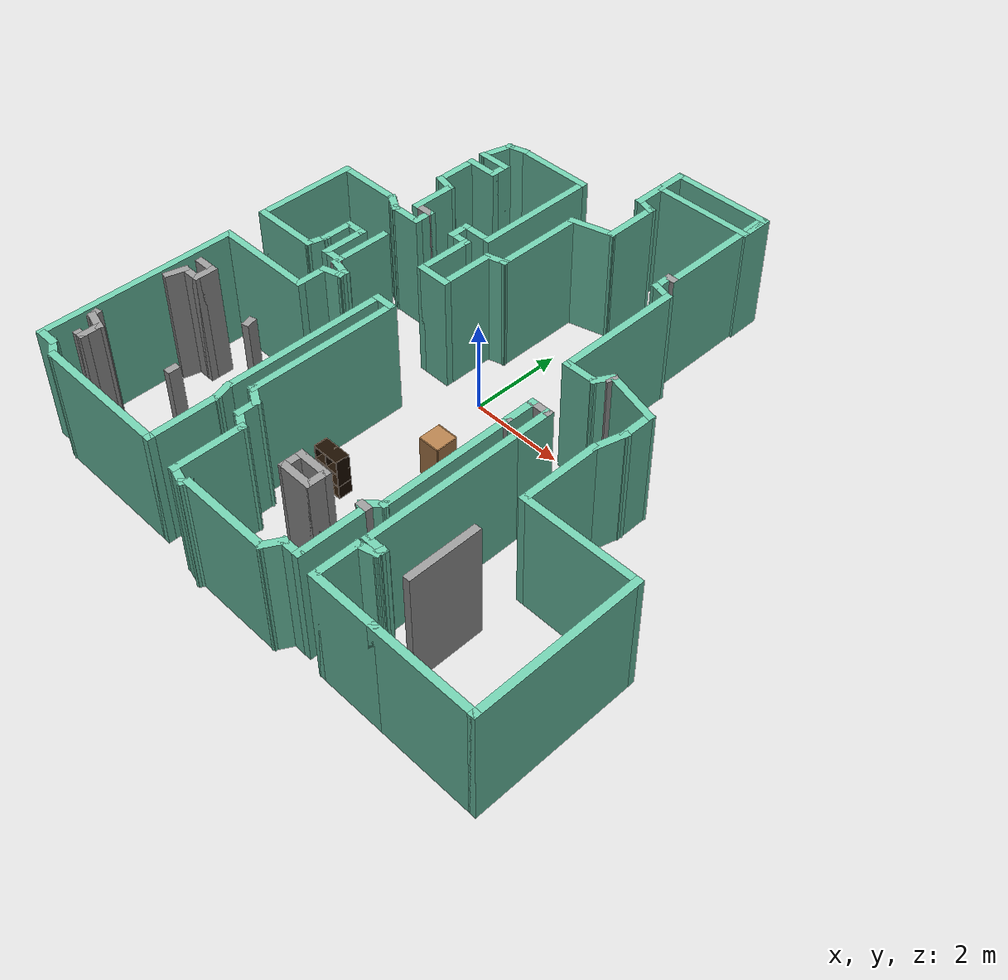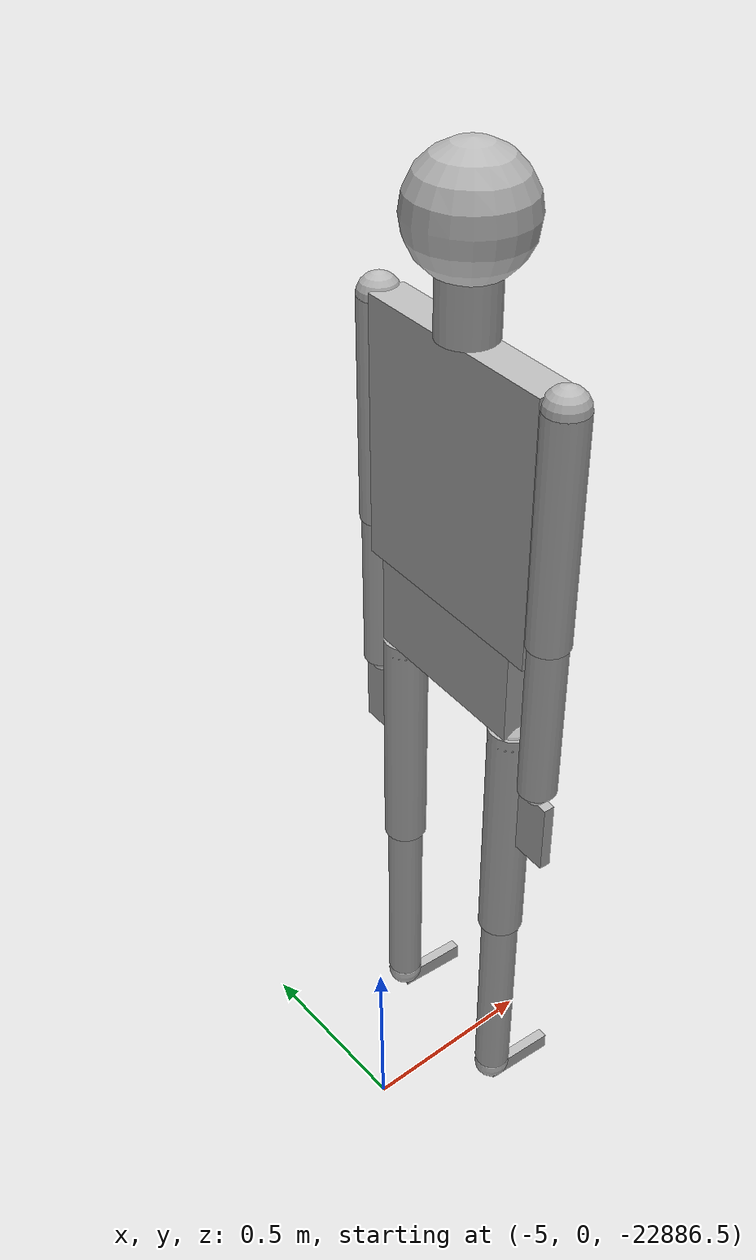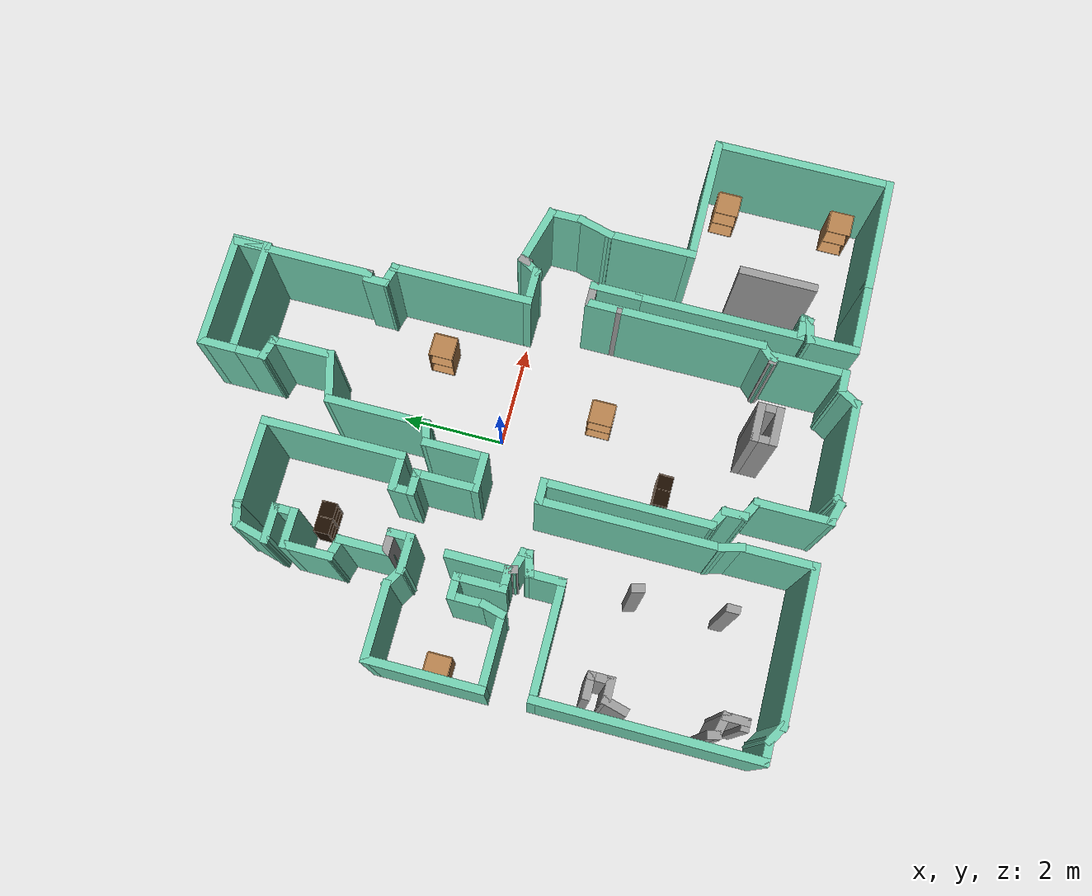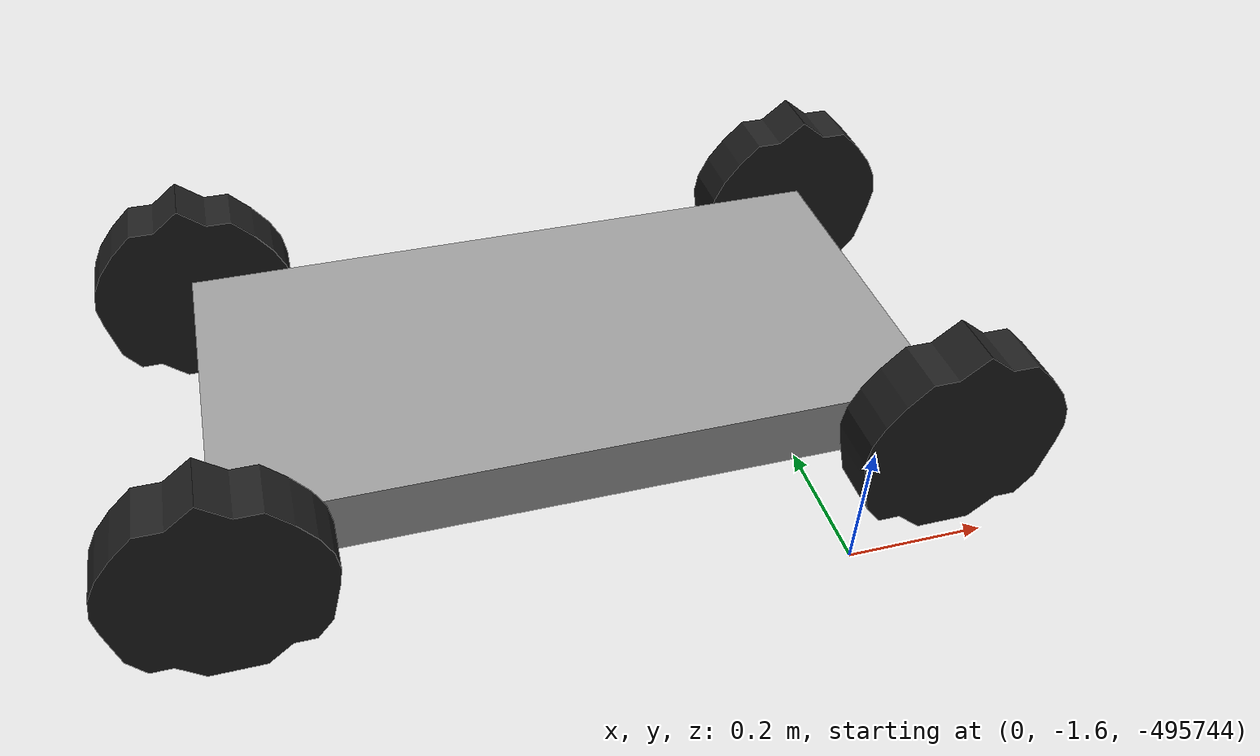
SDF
<sdf version="1.6">
 <world name="default">
  <light name="sun" type="directional">
   <pose>0 0 10 0 -0 0</pose>
   <diffuse>0.8 0.8 0.8 1</diffuse>
   <specular>0.2 0.2 0.2 1</specular>
   <attenuation>
    <range>1000</range>
    <constant>0.9</constant>
    <linear>0.01</linear>
    <quadratic>0.001</quadratic>
   </attenuation>
   <direction>-0.5 0.1 -0.9</direction>
  </light>
  <gravity>0 0 -9.8</gravity>
  <magnetic_field>6e-06 2.3e-05 -4.2e-05</magnetic_field>
  <atmosphere type="adiabatic"/>
  <physics name="default_physics" default="0" type="ode">
   <max_step_size>0.001</max_step_size>
   <real_time_factor>1</real_time_factor>
   <real_time_update_rate>1000</real_time_update_rate>
  </physics>
  <scene><ambient>0.4 0.4 0.4 1</ambient><background>0.7 0.7 0.7 1</background><shadows>1</shadows></scene>
  <audio><device>default</device></audio>
  <spherical_coordinates>
   <surface_model>EARTH_WGS84</surface_model>
   <latitude_deg>0</latitude_deg>
   <longitude_deg>0</longitude_deg>
   <elevation>0</elevation>
   <heading_deg>0</heading_deg>
  </spherical_coordinates>
  <model name="map_3">
   <pose>0.639107 -0.35531 0 0 -0 0</pose>
   <link name="Wall_0">
    <collision name="Wall_0_Collision">
     <geometry><box><size>2.25 0.15 2.5</size></box></geometry>
     <pose>0 0 1.25 0 -0 0</pose>
    </collision>
    <visual name="Wall_0_Visual">
     <pose>0 0 1.25 0 -0 0</pose>
     <geometry><box><size>2.25 0.15 2.5</size></box></geometry>
     <material>
      <script><uri>file://media/materials/scripts/gazebo.material</uri><name>Gazebo/Grey</name></script>
      <ambient>0.435294 0.796078 0.67451 1</ambient>
     </material>
     <meta><layer>0</layer></meta>
    </visual>
    <pose>0.303175 6.04258 0 0 -0 3.14159</pose>
   </link>
   <link name="Wall_1">
    <collision name="Wall_1_Collision">
     <geometry><box><size>0.75 0.15 2.5</size></box></geometry>
     <pose>0 0 1.25 0 -0 0</pose>
    </collision>
    <visual name="Wall_1_Visual">
     <pose>0 0 1.25 0 -0 0</pose>
     <geometry><box><size>0.75 0.15 2.5</size></box></geometry>
     <material>
      <script><uri>file://media/materials/scripts/gazebo.material</uri><name>Gazebo/Grey</name></script>
      <ambient>0.435294 0.796078 0.67451 1</ambient>
     </material>
     <meta><layer>0</layer></meta>
    </visual>
    <pose>-0.746825 5.74258 0 0 -0 -1.5708</pose>
   </link>
   <link name="Wall_10">
    <collision name="Wall_10_Collision">
     <geometry><box><size>0.5 0.15 2.5</size></box></geometry>
     <pose>0 0 1.25 0 -0 0</pose>
    </collision>
    <visual name="Wall_10_Visual">
     <pose>0 0 1.25 0 -0 0</pose>
     <geometry><box><size>0.5 0.15 2.5</size></box></geometry>
     <material>
      <script><uri>file://media/materials/scripts/gazebo.material</uri><name>Gazebo/Grey</name></script>
      <ambient>0.435294 0.796078 0.67451 1</ambient>
     </material>
     <meta><layer>0</layer></meta>
    </visual>
    <pose>-1.39882 1.53671 0 0 -0 -2.87979</pose>
   </link>
   <link name="Wall_100">
    <collision name="Wall_100_Collision">
     <geometry><box><size>1.75 0.15 2.5</size></box></geometry>
     <pose>0 0 1.25 0 -0 0</pose>
    </collision>
    <visual name="Wall_100_Visual">
     <pose>0 0 1.25 0 -0 0</pose>
     <geometry><box><size>1.75 0.15 2.5</size></box></geometry>
     <material>
      <script><uri>file://media/materials/scripts/gazebo.material</uri><name>Gazebo/Grey</name></script>
      <ambient>0.435294 0.796078 0.67451 1</ambient>
     </material>
     <meta><layer>0</layer></meta>
    </visual>
    <pose>3.22626 -1.57739 0 0 -0 1.5708</pose>
   </link>
   <link name="Wall_101">
    <collision name="Wall_101_Collision">
     <geometry><box><size>0.75 0.15 2.5</size></box></geometry>
     <pose>0 0 1.25 0 -0 0</pose>
    </collision>
    <visual name="Wall_101_Visual">
     <pose>0 0 1.25 0 -0 0</pose>
     <geometry><box><size>0.75 0.15 2.5</size></box></geometry>
     <material>
      <script><uri>file://media/materials/scripts/gazebo.material</uri><name>Gazebo/Grey</name></script>
      <ambient>0.435294 0.796078 0.67451 1</ambient>
     </material>
     <meta><layer>0</layer></meta>
    </visual>
    <pose>3.30391 -0.487613 0 0 -0 1.309</pose>
   </link>
   <link name="Wall_102">
    <collision name="Wall_102_Collision">
     <geometry><box><size>0.75 0.15 2.5</size></box></geometry>
     <pose>0 0 1.25 0 -0 0</pose>
    </collision>
    <visual name="Wall_102_Visual">
     <pose>0 0 1.25 0 -0 0</pose>
     <geometry><box><size>0.75 0.15 2.5</size></box></geometry>
     <material>
      <script><uri>file://media/materials/scripts/gazebo.material</uri><name>Gazebo/Grey</name></script>
      <ambient>0.435294 0.796078 0.67451 1</ambient>
     </material>
     <meta><layer>0</layer></meta>
    </visual>
    <pose>3.38155 0.102165 0 0 -0 1.5708</pose>
   </link>
   <link name="Wall_103">
    <collision name="Wall_103_Collision">
     <geometry><box><size>1.25 0.15 2.5</size></box></geometry>
     <pose>0 0 1.25 0 -0 0</pose>
    </collision>
    <visual name="Wall_103_Visual">
     <pose>0 0 1.25 0 -0 0</pose>
     <geometry><box><size>1.25 0.15 2.5</size></box></geometry>
     <material>
      <script><uri>file://media/materials/scripts/gazebo.material</uri><name>Gazebo/Grey</name></script>
      <ambient>0.435294 0.796078 0.67451 1</ambient>
     </material>
     <meta><layer>0</layer></meta>
    </visual>
    <pose>2.85029 0.544515 0 0 -0 2.87979</pose>
   </link>
   <link name="Wall_104">
    <collision name="Wall_104_Collision">
     <geometry><box><size>0.25 0.15 2.5</size></box></geometry>
     <pose>0 0 1.25 0 -0 0</pose>
    </collision>
    <visual name="Wall_104_Visual">
     <pose>0 0 1.25 0 -0 0</pose>
     <geometry><box><size>0.25 0.15 2.5</size></box></geometry>
     <material>
      <script><uri>file://media/materials/scripts/gazebo.material</uri><name>Gazebo/Grey</name></script>
      <ambient>1 1 1 1</ambient>
     </material>
     <meta><layer>0</layer></meta>
    </visual>
    <pose>2.30609 0.638569 0 0 -0 -1.8326</pose>
   </link>
   <link name="Wall_108">
    <collision name="Wall_108_Collision">
     <geometry><box><size>0.5 0.15 2.5</size></box></geometry>
     <pose>0 0 1.25 0 -0 0</pose>
    </collision>
    <visual name="Wall_108_Visual">
     <pose>0 0 1.25 0 -0 0</pose>
     <geometry><box><size>0.5 0.15 2.5</size></box></geometry>
     <material>
      <script><uri>file://media/materials/scripts/gazebo.material</uri><name>Gazebo/Grey</name></script>
      <ambient>0.435294 0.796078 0.67451 1</ambient>
     </material>
     <meta><layer>0</layer></meta>
    </visual>
    <pose>2.23154 0.535311 0 0 -0 -2.0944</pose>
   </link>
   <link name="Wall_109">
    <collision name="Wall_109_Collision">
     <geometry><box><size>0.75 0.15 2.5</size></box></geometry>
     <pose>0 0 1.25 0 -0 0</pose>
    </collision>
    <visual name="Wall_109_Visual">
     <pose>0 0 1.25 0 -0 0</pose>
     <geometry><box><size>0.75 0.15 2.5</size></box></geometry>
     <material>
      <script><uri>file://media/materials/scripts/gazebo.material</uri><name>Gazebo/Grey</name></script>
      <ambient>0.435294 0.796078 0.67451 1</ambient>
     </material>
     <meta><layer>0</layer></meta>
    </visual>
    <pose>1.84404 0.383757 0 0 -0 3.14159</pose>
   </link>
   <link name="Wall_11">
    <collision name="Wall_11_Collision">
     <geometry><box><size>1.25 0.15 2.5</size></box></geometry>
     <pose>0 0 1.25 0 -0 0</pose>
    </collision>
    <visual name="Wall_11_Visual">
     <pose>0 0 1.25 0 -0 0</pose>
     <geometry><box><size>1.25 0.15 2.5</size></box></geometry>
     <material>
      <script><uri>file://media/materials/scripts/gazebo.material</uri><name>Gazebo/Grey</name></script>
      <ambient>0.435294 0.796078 0.67451 1</ambient>
     </material>
     <meta><layer>0</layer></meta>
    </visual>
    <pose>-1.56786 0.941415 0 0 -0 -1.5708</pose>
   </link>
   <link name="Wall_110">
    <collision name="Wall_110_Collision">
     <geometry><box><size>2.75 0.15 2.5</size></box></geometry>
     <pose>0 0 1.25 0 -0 0</pose>
    </collision>
    <visual name="Wall_110_Visual">
     <pose>0 0 1.25 0 -0 0</pose>
     <geometry><box><size>2.75 0.15 2.5</size></box></geometry>
     <material>
      <script><uri>file://media/materials/scripts/gazebo.material</uri><name>Gazebo/Grey</name></script>
      <ambient>0.435294 0.796078 0.67451 1</ambient>
     </material>
     <meta><layer>0</layer></meta>
    </visual>
    <pose>1.54404 1.68376 0 0 -0 1.5708</pose>
   </link>
   <link name="Wall_111">
    <collision name="Wall_111_Collision">
     <geometry><box><size>0.5 0.15 2.5</size></box></geometry>
     <pose>0 0 1.25 0 -0 0</pose>
    </collision>
    <visual name="Wall_111_Visual">
     <pose>0 0 1.25 0 -0 0</pose>
     <geometry><box><size>0.5 0.15 2.5</size></box></geometry>
     <material>
      <script><uri>file://media/materials/scripts/gazebo.material</uri><name>Gazebo/Grey</name></script>
      <ambient>0.435294 0.796078 0.67451 1</ambient>
     </material>
     <meta><layer>0</layer></meta>
    </visual>
    <pose>1.375 3.02905 0 0 -0 2.87979</pose>
   </link>
   <link name="Wall_112">
    <collision name="Wall_112_Collision">
     <geometry><box><size>0.5 0.15 2.5</size></box></geometry>
     <pose>0 0 1.25 0 -0 0</pose>
    </collision>
    <visual name="Wall_112_Visual">
     <pose>0 0 1.25 0 -0 0</pose>
     <geometry><box><size>0.5 0.15 2.5</size></box></geometry>
     <material>
      <script><uri>file://media/materials/scripts/gazebo.material</uri><name>Gazebo/Grey</name></script>
      <ambient>0.435294 0.796078 0.67451 1</ambient>
     </material>
     <meta><layer>0</layer></meta>
    </visual>
    <pose>1.20596 3.24934 0 0 -0 1.5708</pose>
   </link>
   <link name="Wall_113">
    <collision name="Wall_113_Collision">
     <geometry><box><size>0.25 0.15 2.5</size></box></geometry>
     <pose>0 0 1.25 0 -0 0</pose>
    </collision>
    <visual name="Wall_113_Visual">
     <pose>0 0 1.25 0 -0 0</pose>
     <geometry><box><size>0.25 0.15 2.5</size></box></geometry>
     <material>
      <script><uri>file://media/materials/scripts/gazebo.material</uri><name>Gazebo/Grey</name></script>
      <ambient>1 1 1 1</ambient>
     </material>
     <meta><layer>0</layer></meta>
    </visual>
    <pose>1.25596 3.42434 0 0 -0 0</pose>
   </link>
   <link name="Wall_114">
    <collision name="Wall_114_Collision">
     <geometry><box><size>2.75 0.15 2.5</size></box></geometry>
     <pose>0 0 1.25 0 -0 0</pose>
    </collision>
    <visual name="Wall_114_Visual">
     <pose>0 0 1.25 0 -0 0</pose>
     <geometry><box><size>2.75 0.15 2.5</size></box></geometry>
     <material>
      <script><uri>file://media/materials/scripts/gazebo.material</uri><name>Gazebo/Grey</name></script>
      <ambient>0.435294 0.796078 0.67451 1</ambient>
     </material>
     <meta><layer>0</layer></meta>
    </visual>
    <pose>1.30596 4.72434 0 0 -0 1.5708</pose>
   </link>
   <link name="Wall_12">
    <collision name="Wall_12_Collision">
     <geometry><box><size>0.75 0.15 2.5</size></box></geometry>
     <pose>0 0 1.25 0 -0 0</pose>
    </collision>
    <visual name="Wall_12_Visual">
     <pose>0 0 1.25 0 -0 0</pose>
     <geometry><box><size>0.75 0.15 2.5</size></box></geometry>
     <material>
      <script><uri>file://media/materials/scripts/gazebo.material</uri><name>Gazebo/Grey</name></script>
      <ambient>0.435294 0.796078 0.67451 1</ambient>
     </material>
     <meta><layer>0</layer></meta>
    </visual>
    <pose>-1.86786 0.391415 0 0 -0 3.14159</pose>
   </link>
   <link name="Wall_125">
    <collision name="Wall_125_Collision">
     <geometry><box><size>0.5 0.15 2.5</size></box></geometry>
     <pose>0 0 1.25 0 -0 0</pose>
    </collision>
    <visual name="Wall_125_Visual">
     <pose>0 0 1.25 0 -0 0</pose>
     <geometry><box><size>0.5 0.15 2.5</size></box></geometry>
     <material>
      <script><uri>file://media/materials/scripts/gazebo.material</uri><name>Gazebo/Grey</name></script>
      <ambient>1 1 1 1</ambient>
     </material>
     <meta><layer>0</layer></meta>
    </visual>
    <pose>0.031075 -4.44181 0 0 -0 -1.5708</pose>
   </link>
   <link name="Wall_126">
    <collision name="Wall_126_Collision">
     <geometry><box><size>0.75 0.15 2.5</size></box></geometry>
     <pose>0 0 1.25 0 -0 0</pose>
    </collision>
    <visual name="Wall_126_Visual">
     <pose>0 0 1.25 0 -0 0</pose>
     <geometry><box><size>0.75 0.15 2.5</size></box></geometry>
     <material>
      <script><uri>file://media/materials/scripts/gazebo.material</uri><name>Gazebo/Grey</name></script>
      <ambient>1 1 1 1</ambient>
     </material>
     <meta><layer>0</layer></meta>
    </visual>
    <pose>0.331075 -4.61681 0 0 -0 0</pose>
   </link>
   <link name="Wall_127">
    <collision name="Wall_127_Collision">
     <geometry><box><size>0.5 0.15 2.5</size></box></geometry>
     <pose>0 0 1.25 0 -0 0</pose>
    </collision>
    <visual name="Wall_127_Visual">
     <pose>0 0 1.25 0 -0 0</pose>
     <geometry><box><size>0.5 0.15 2.5</size></box></geometry>
     <material>
      <script><uri>file://media/materials/scripts/gazebo.material</uri><name>Gazebo/Grey</name></script>
      <ambient>1 1 1 1</ambient>
     </material>
     <meta><layer>0</layer></meta>
    </visual>
    <pose>0.631075 -4.44181 0 0 -0 1.5708</pose>
   </link>
   <link name="Wall_128">
    <collision name="Wall_128_Collision">
     <geometry><box><size>0.75 0.15 2.5</size></box></geometry>
     <pose>0 0 1.25 0 -0 0</pose>
    </collision>
    <visual name="Wall_128_Visual">
     <pose>0 0 1.25 0 -0 0</pose>
     <geometry><box><size>0.75 0.15 2.5</size></box></geometry>
     <material>
      <script><uri>file://media/materials/scripts/gazebo.material</uri><name>Gazebo/Grey</name></script>
      <ambient>1 1 1 1</ambient>
     </material>
     <meta><layer>0</layer></meta>
    </visual>
    <pose>0.331075 -4.26681 0 0 -0 3.14159</pose>
   </link>
   <link name="Wall_130">
    <collision name="Wall_130_Collision">
     <geometry><box><size>1.5 0.15 2.5</size></box></geometry>
     <pose>0 0 1.25 0 -0 0</pose>
    </collision>
    <visual name="Wall_130_Visual">
     <pose>0 0 1.25 0 -0 0</pose>
     <geometry><box><size>1.5 0.15 2.5</size></box></geometry>
     <material>
      <script><uri>file://media/materials/scripts/gazebo.material</uri><name>Gazebo/Grey</name></script>
      <ambient>1 1 1 1</ambient>
     </material>
     <meta><layer>0</layer></meta>
    </visual>
    <pose>3.15108 -4.06181 0 0 -0 -1.5708</pose>
   </link>
   <link name="Wall_132">
    <collision name="Wall_132_Collision">
     <geometry><box><size>0.25 0.15 2.5</size></box></geometry>
     <pose>0 0 1.25 0 -0 0</pose>
    </collision>
    <visual name="Wall_132_Visual">
     <pose>0 0 1.25 0 -0 0</pose>
     <geometry><box><size>0.25 0.15 2.5</size></box></geometry>
     <material>
      <script><uri>file://media/materials/scripts/gazebo.material</uri><name>Gazebo/Grey</name></script>
      <ambient>1 1 1 1</ambient>
     </material>
     <meta><layer>0</layer></meta>
    </visual>
    <pose>-3.17598 -2.85511 0 0 -0 -1.309</pose>
   </link>
   <link name="Wall_134">
    <collision name="Wall_134_Collision">
     <geometry><box><size>0.25 0.15 2.5</size></box></geometry>
     <pose>0 0 1.25 0 -0 0</pose>
    </collision>
    <visual name="Wall_134_Visual">
     <pose>0 0 1.25 0 -0 0</pose>
     <geometry><box><size>0.25 0.15 2.5</size></box></geometry>
     <material>
      <script><uri>file://media/materials/scripts/gazebo.material</uri><name>Gazebo/Grey</name></script>
      <ambient>1 1 1 1</ambient>
     </material>
     <meta><layer>0</layer></meta>
    </visual>
    <pose>-3.10893 -4.55681 0 0 -0 -1.5708</pose>
   </link>
   <link name="Wall_138">
    <collision name="Wall_138_Collision">
     <geometry><box><size>0.5 0.15 2.5</size></box></geometry>
     <pose>0 0 1.25 0 -0 0</pose>
    </collision>
    <visual name="Wall_138_Visual">
     <pose>0 0 1.25 0 -0 0</pose>
     <geometry><box><size>0.5 0.15 2.5</size></box></geometry>
     <material>
      <script><uri>file://media/materials/scripts/gazebo.material</uri><name>Gazebo/Grey</name></script>
      <ambient>1 1 1 1</ambient>
     </material>
     <meta><layer>0</layer></meta>
    </visual>
    <pose>-5.02718 -2.4211 0 0 -0 0</pose>
   </link>
   <link name="Wall_139">
    <collision name="Wall_139_Collision">
     <geometry><box><size>0.5 0.15 2.5</size></box></geometry>
     <pose>0 0 1.25 0 -0 0</pose>
    </collision>
    <visual name="Wall_139_Visual">
     <pose>0 0 1.25 0 -0 0</pose>
     <geometry><box><size>0.5 0.15 2.5</size></box></geometry>
     <material>
      <script><uri>file://media/materials/scripts/gazebo.material</uri><name>Gazebo/Grey</name></script>
      <ambient>1 1 1 1</ambient>
     </material>
     <meta><layer>0</layer></meta>
    </visual>
    <pose>-4.85218 -2.5961 0 0 -0 -1.5708</pose>
   </link>
   <link name="Wall_140">
    <collision name="Wall_140_Collision">
     <geometry><box><size>0.5 0.15 2.5</size></box></geometry>
     <pose>0 0 1.25 0 -0 0</pose>
    </collision>
    <visual name="Wall_140_Visual">
     <pose>0 0 1.25 0 -0 0</pose>
     <geometry><box><size>0.5 0.15 2.5</size></box></geometry>
     <material>
      <script><uri>file://media/materials/scripts/gazebo.material</uri><name>Gazebo/Grey</name></script>
      <ambient>1 1 1 1</ambient>
     </material>
     <meta><layer>0</layer></meta>
    </visual>
    <pose>-5.02718 -2.7711 0 0 -0 3.14159</pose>
   </link>
   <link name="Wall_141">
    <collision name="Wall_141_Collision">
     <geometry><box><size>0.5 0.15 2.5</size></box></geometry>
     <pose>0 0 1.25 0 -0 0</pose>
    </collision>
    <visual name="Wall_141_Visual">
     <pose>0 0 1.25 0 -0 0</pose>
     <geometry><box><size>0.5 0.15 2.5</size></box></geometry>
     <material>
      <script><uri>file://media/materials/scripts/gazebo.material</uri><name>Gazebo/Grey</name></script>
      <ambient>1 1 1 1</ambient>
     </material>
     <meta><layer>0</layer></meta>
    </visual>
    <pose>-5.24747 -2.94014 0 0 -0 -1.8326</pose>
   </link>
   <link name="Wall_144">
    <collision name="Wall_144_Collision">
     <geometry><box><size>0.25 0.15 2.5</size></box></geometry>
     <pose>0 0 1.25 0 -0 0</pose>
    </collision>
    <visual name="Wall_144_Visual">
     <pose>0 0 1.25 0 -0 0</pose>
     <geometry><box><size>0.25 0.15 2.5</size></box></geometry>
     <material>
      <script><uri>file://media/materials/scripts/gazebo.material</uri><name>Gazebo/Grey</name></script>
      <ambient>1 1 1 1</ambient>
     </material>
     <meta><layer>0</layer></meta>
    </visual>
    <pose>-5.28923 -4.6894 0 0 -0 -1.309</pose>
   </link>
   <link name="Wall_145">
    <collision name="Wall_145_Collision">
     <geometry><box><size>0.5 0.15 2.5</size></box></geometry>
     <pose>0 0 1.25 0 -0 0</pose>
    </collision>
    <visual name="Wall_145_Visual">
     <pose>0 0 1.25 0 -0 0</pose>
     <geometry><box><size>0.5 0.15 2.5</size></box></geometry>
     <material>
      <script><uri>file://media/materials/scripts/gazebo.material</uri><name>Gazebo/Grey</name></script>
      <ambient>1 1 1 1</ambient>
     </material>
     <meta><layer>0</layer></meta>
    </visual>
    <pose>-5.10726 -4.78299 0 0 -0 -0.261799</pose>
   </link>
   <link name="Wall_146">
    <collision name="Wall_146_Collision">
     <geometry><box><size>0.5 0.15 2.5</size></box></geometry>
     <pose>0 0 1.25 0 -0 0</pose>
    </collision>
    <visual name="Wall_146_Visual">
     <pose>0 0 1.25 0 -0 0</pose>
     <geometry><box><size>0.5 0.15 2.5</size></box></geometry>
     <material>
      <script><uri>file://media/materials/scripts/gazebo.material</uri><name>Gazebo/Grey</name></script>
      <ambient>1 1 1 1</ambient>
     </material>
     <meta><layer>0</layer></meta>
    </visual>
    <pose>-4.93822 -5.00328 0 0 -0 -1.5708</pose>
   </link>
   <link name="Wall_147">
    <collision name="Wall_147_Collision">
     <geometry><box><size>0.25 0.15 2.5</size></box></geometry>
     <pose>0 0 1.25 0 -0 0</pose>
    </collision>
    <visual name="Wall_147_Visual">
     <pose>0 0 1.25 0 -0 0</pose>
     <geometry><box><size>0.25 0.15 2.5</size></box></geometry>
     <material>
      <script><uri>file://media/materials/scripts/gazebo.material</uri><name>Gazebo/Grey</name></script>
      <ambient>1 1 1 1</ambient>
     </material>
     <meta><layer>0</layer></meta>
    </visual>
    <pose>-4.98822 -5.17828 0 0 -0 3.14159</pose>
   </link>
   <link name="Wall_18">
    <collision name="Wall_18_Collision">
     <geometry><box><size>1.25 0.15 2.5</size></box></geometry>
     <pose>0 0 1.25 0 -0 0</pose>
    </collision>
    <visual name="Wall_18_Visual">
     <pose>0 0 1.25 0 -0 0</pose>
     <geometry><box><size>1.25 0.15 2.5</size></box></geometry>
     <material>
      <script><uri>file://media/materials/scripts/gazebo.material</uri><name>Gazebo/Grey</name></script>
      <ambient>0.435294 0.796078 0.67451 1</ambient>
     </material>
     <meta><layer>0</layer></meta>
    </visual>
    <pose>-2.16786 0.941415 0 0 -0 1.5708</pose>
   </link>
   <link name="Wall_19">
    <collision name="Wall_19_Collision">
     <geometry><box><size>0.5 0.15 2.5</size></box></geometry>
     <pose>0 0 1.25 0 -0 0</pose>
    </collision>
    <visual name="Wall_19_Visual">
     <pose>0 0 1.25 0 -0 0</pose>
     <geometry><box><size>0.5 0.15 2.5</size></box></geometry>
     <material>
      <script><uri>file://media/materials/scripts/gazebo.material</uri><name>Gazebo/Grey</name></script>
      <ambient>0.435294 0.796078 0.67451 1</ambient>
     </material>
     <meta><layer>0</layer></meta>
    </visual>
    <pose>-2.34286 1.49141 0 0 -0 3.14159</pose>
   </link>
   <link name="Wall_2">
    <collision name="Wall_2_Collision">
     <geometry><box><size>2.25 0.15 2.5</size></box></geometry>
     <pose>0 0 1.25 0 -0 0</pose>
    </collision>
    <visual name="Wall_2_Visual">
     <pose>0 0 1.25 0 -0 0</pose>
     <geometry><box><size>2.25 0.15 2.5</size></box></geometry>
     <material>
      <script><uri>file://media/materials/scripts/gazebo.material</uri><name>Gazebo/Grey</name></script>
      <ambient>0.435294 0.796078 0.67451 1</ambient>
     </material>
     <meta><layer>0</layer></meta>
    </visual>
    <pose>0.303175 5.44259 0 0 -0 0</pose>
   </link>
   <link name="Wall_22">
    <collision name="Wall_22_Collision">
     <geometry><box><size>0.5 0.15 2.5</size></box></geometry>
     <pose>0 0 1.25 0 -0 0</pose>
    </collision>
    <visual name="Wall_22_Visual">
     <pose>0 0 1.25 0 -0 0</pose>
     <geometry><box><size>0.5 0.15 2.5</size></box></geometry>
     <material>
      <script><uri>file://media/materials/scripts/gazebo.material</uri><name>Gazebo/Grey</name></script>
      <ambient>0.435294 0.796078 0.67451 1</ambient>
     </material>
     <meta><layer>0</layer></meta>
    </visual>
    <pose>-2.51786 1.66641 0 0 -0 1.5708</pose>
   </link>
   <link name="Wall_23">
    <collision name="Wall_23_Collision">
     <geometry><box><size>0.75 0.15 2.5</size></box></geometry>
     <pose>0 0 1.25 0 -0 0</pose>
    </collision>
    <visual name="Wall_23_Visual">
     <pose>0 0 1.25 0 -0 0</pose>
     <geometry><box><size>0.75 0.15 2.5</size></box></geometry>
     <material>
      <script><uri>file://media/materials/scripts/gazebo.material</uri><name>Gazebo/Grey</name></script>
      <ambient>0.435294 0.796078 0.67451 1</ambient>
     </material>
     <meta><layer>0</layer></meta>
    </visual>
    <pose>-2.21786 1.84142 0 0 -0 0</pose>
   </link>
   <link name="Wall_24">
    <collision name="Wall_24_Collision">
     <geometry><box><size>2.75 0.15 2.5</size></box></geometry>
     <pose>0 0 1.25 0 -0 0</pose>
    </collision>
    <visual name="Wall_24_Visual">
     <pose>0 0 1.25 0 -0 0</pose>
     <geometry><box><size>2.75 0.15 2.5</size></box></geometry>
     <material>
      <script><uri>file://media/materials/scripts/gazebo.material</uri><name>Gazebo/Grey</name></script>
      <ambient>0.435294 0.796078 0.67451 1</ambient>
     </material>
     <meta><layer>0</layer></meta>
    </visual>
    <pose>-1.91786 3.14141 0 0 -0 1.5708</pose>
   </link>
   <link name="Wall_25">
    <collision name="Wall_25_Collision">
     <geometry><box><size>1.75 0.15 2.5</size></box></geometry>
     <pose>0 0 1.25 0 -0 0</pose>
    </collision>
    <visual name="Wall_25_Visual">
     <pose>0 0 1.25 0 -0 0</pose>
     <geometry><box><size>1.75 0.15 2.5</size></box></geometry>
     <material>
      <script><uri>file://media/materials/scripts/gazebo.material</uri><name>Gazebo/Grey</name></script>
      <ambient>0.435294 0.796078 0.67451 1</ambient>
     </material>
     <meta><layer>0</layer></meta>
    </visual>
    <pose>-2.71786 4.44142 0 0 -0 3.14159</pose>
   </link>
   <link name="Wall_26">
    <collision name="Wall_26_Collision">
     <geometry><box><size>0.5 0.15 2.5</size></box></geometry>
     <pose>0 0 1.25 0 -0 0</pose>
    </collision>
    <visual name="Wall_26_Visual">
     <pose>0 0 1.25 0 -0 0</pose>
     <geometry><box><size>0.5 0.15 2.5</size></box></geometry>
     <material>
      <script><uri>file://media/materials/scripts/gazebo.material</uri><name>Gazebo/Grey</name></script>
      <ambient>0.435294 0.796078 0.67451 1</ambient>
     </material>
     <meta><layer>0</layer></meta>
    </visual>
    <pose>-3.6869 4.39612 0 0 -0 -2.87979</pose>
   </link>
   <link name="Wall_27">
    <collision name="Wall_27_Collision">
     <geometry><box><size>0.75 0.15 2.5</size></box></geometry>
     <pose>0 0 1.25 0 -0 0</pose>
    </collision>
    <visual name="Wall_27_Visual">
     <pose>0 0 1.25 0 -0 0</pose>
     <geometry><box><size>0.75 0.15 2.5</size></box></geometry>
     <material>
      <script><uri>file://media/materials/scripts/gazebo.material</uri><name>Gazebo/Grey</name></script>
      <ambient>0.435294 0.796078 0.67451 1</ambient>
     </material>
     <meta><layer>0</layer></meta>
    </visual>
    <pose>-3.93358 4.06105 0 0 -0 -1.8326</pose>
   </link>
   <link name="Wall_28">
    <collision name="Wall_28_Collision">
     <geometry><box><size>0.75 0.15 2.5</size></box></geometry>
     <pose>0 0 1.25 0 -0 0</pose>
    </collision>
    <visual name="Wall_28_Visual">
     <pose>0 0 1.25 0 -0 0</pose>
     <geometry><box><size>0.75 0.15 2.5</size></box></geometry>
     <material>
      <script><uri>file://media/materials/scripts/gazebo.material</uri><name>Gazebo/Grey</name></script>
      <ambient>0.435294 0.796078 0.67451 1</ambient>
     </material>
     <meta><layer>0</layer></meta>
    </visual>
    <pose>-3.71123 3.77127 0 0 -0 0</pose>
   </link>
   <link name="Wall_29">
    <collision name="Wall_29_Collision">
     <geometry><box><size>0.5 0.15 2.5</size></box></geometry>
     <pose>0 0 1.25 0 -0 0</pose>
    </collision>
    <visual name="Wall_29_Visual">
     <pose>0 0 1.25 0 -0 0</pose>
     <geometry><box><size>0.5 0.15 2.5</size></box></geometry>
     <material>
      <script><uri>file://media/materials/scripts/gazebo.material</uri><name>Gazebo/Grey</name></script>
      <ambient>0.435294 0.796078 0.67451 1</ambient>
     </material>
     <meta><layer>0</layer></meta>
    </visual>
    <pose>-3.41123 3.59627 0 0 -0 -1.5708</pose>
   </link>
   <link name="Wall_3">
    <collision name="Wall_3_Collision">
     <geometry><box><size>0.75 0.15 2.5</size></box></geometry>
     <pose>0 0 1.25 0 -0 0</pose>
    </collision>
    <visual name="Wall_3_Visual">
     <pose>0 0 1.25 0 -0 0</pose>
     <geometry><box><size>0.75 0.15 2.5</size></box></geometry>
     <material>
      <script><uri>file://media/materials/scripts/gazebo.material</uri><name>Gazebo/Grey</name></script>
      <ambient>0.435294 0.796078 0.67451 1</ambient>
     </material>
     <meta><layer>0</layer></meta>
    </visual>
    <pose>1.35318 5.74258 0 0 -0 1.5708</pose>
   </link>
   <link name="Wall_30">
    <collision name="Wall_30_Collision">
     <geometry><box><size>0.75 0.15 2.5</size></box></geometry>
     <pose>0 0 1.25 0 -0 0</pose>
    </collision>
    <visual name="Wall_30_Visual">
     <pose>0 0 1.25 0 -0 0</pose>
     <geometry><box><size>0.75 0.15 2.5</size></box></geometry>
     <material>
      <script><uri>file://media/materials/scripts/gazebo.material</uri><name>Gazebo/Grey</name></script>
      <ambient>0.435294 0.796078 0.67451 1</ambient>
     </material>
     <meta><layer>0</layer></meta>
    </visual>
    <pose>-3.71123 3.42127 0 0 -0 3.14159</pose>
   </link>
   <link name="Wall_31">
    <collision name="Wall_31_Collision">
     <geometry><box><size>1 0.15 2.5</size></box></geometry>
     <pose>0 0 1.25 0 -0 0</pose>
    </collision>
    <visual name="Wall_31_Visual">
     <pose>0 0 1.25 0 -0 0</pose>
     <geometry><box><size>1 0.15 2.5</size></box></geometry>
     <material>
      <script><uri>file://media/materials/scripts/gazebo.material</uri><name>Gazebo/Grey</name></script>
      <ambient>0.435294 0.796078 0.67451 1</ambient>
     </material>
     <meta><layer>0</layer></meta>
    </visual>
    <pose>-4.01123 2.99627 0 0 -0 -1.5708</pose>
   </link>
   <link name="Wall_32">
    <collision name="Wall_32_Collision">
     <geometry><box><size>0.5 0.15 2.5</size></box></geometry>
     <pose>0 0 1.25 0 -0 0</pose>
    </collision>
    <visual name="Wall_32_Visual">
     <pose>0 0 1.25 0 -0 0</pose>
     <geometry><box><size>0.5 0.15 2.5</size></box></geometry>
     <material>
      <script><uri>file://media/materials/scripts/gazebo.material</uri><name>Gazebo/Grey</name></script>
      <ambient>0.435294 0.796078 0.67451 1</ambient>
     </material>
     <meta><layer>0</layer></meta>
    </visual>
    <pose>-3.84219 2.52598 0 0 -0 -0.261799</pose>
   </link>
   <link name="Wall_33">
    <collision name="Wall_33_Collision">
     <geometry><box><size>1 0.15 2.5</size></box></geometry>
     <pose>0 0 1.25 0 -0 0</pose>
    </collision>
    <visual name="Wall_33_Visual">
     <pose>0 0 1.25 0 -0 0</pose>
     <geometry><box><size>1 0.15 2.5</size></box></geometry>
     <material>
      <script><uri>file://media/materials/scripts/gazebo.material</uri><name>Gazebo/Grey</name></script>
      <ambient>0.435294 0.796078 0.67451 1</ambient>
     </material>
     <meta><layer>0</layer></meta>
    </visual>
    <pose>-3.67315 2.05569 0 0 -0 -1.5708</pose>
   </link>
   <link name="Wall_34">
    <collision name="Wall_34_Collision">
     <geometry><box><size>0.5 0.15 2.5</size></box></geometry>
     <pose>0 0 1.25 0 -0 0</pose>
    </collision>
    <visual name="Wall_34_Visual">
     <pose>0 0 1.25 0 -0 0</pose>
     <geometry><box><size>0.5 0.15 2.5</size></box></geometry>
     <material>
      <script><uri>file://media/materials/scripts/gazebo.material</uri><name>Gazebo/Grey</name></script>
      <ambient>1 1 1 1</ambient>
     </material>
     <meta><layer>0</layer></meta>
    </visual>
    <pose>-3.49815 1.63069 0 0 -0 0</pose>
   </link>
   <link name="Wall_35">
    <collision name="Wall_35_Collision">
     <geometry><box><size>0.5 0.15 2.5</size></box></geometry>
     <pose>0 0 1.25 0 -0 0</pose>
    </collision>
    <visual name="Wall_35_Visual">
     <pose>0 0 1.25 0 -0 0</pose>
     <geometry><box><size>0.5 0.15 2.5</size></box></geometry>
     <material>
      <script><uri>file://media/materials/scripts/gazebo.material</uri><name>Gazebo/Grey</name></script>
      <ambient>0.435294 0.796078 0.67451 1</ambient>
     </material>
     <meta><layer>0</layer></meta>
    </visual>
    <pose>-3.32315 1.45569 0 0 -0 -1.5708</pose>
   </link>
   <link name="Wall_36">
    <collision name="Wall_36_Collision">
     <geometry><box><size>0.75 0.15 2.5</size></box></geometry>
     <pose>0 0 1.25 0 -0 0</pose>
    </collision>
    <visual name="Wall_36_Visual">
     <pose>0 0 1.25 0 -0 0</pose>
     <geometry><box><size>0.75 0.15 2.5</size></box></geometry>
     <material>
      <script><uri>file://media/materials/scripts/gazebo.material</uri><name>Gazebo/Grey</name></script>
      <ambient>0.435294 0.796078 0.67451 1</ambient>
     </material>
     <meta><layer>0</layer></meta>
    </visual>
    <pose>-3.62315 1.28069 0 0 -0 3.14159</pose>
   </link>
   <link name="Wall_37">
    <collision name="Wall_37_Collision">
     <geometry><box><size>0.5 0.15 2.5</size></box></geometry>
     <pose>0 0 1.25 0 -0 0</pose>
    </collision>
    <visual name="Wall_37_Visual">
     <pose>0 0 1.25 0 -0 0</pose>
     <geometry><box><size>0.5 0.15 2.5</size></box></geometry>
     <material>
      <script><uri>file://media/materials/scripts/gazebo.material</uri><name>Gazebo/Grey</name></script>
      <ambient>0.435294 0.796078 0.67451 1</ambient>
     </material>
     <meta><layer>0</layer></meta>
    </visual>
    <pose>-4.07471 1.36819 0 0 -0 2.61799</pose>
   </link>
   <link name="Wall_38">
    <collision name="Wall_38_Collision">
     <geometry><box><size>1.5 0.15 2.5</size></box></geometry>
     <pose>0 0 1.25 0 -0 0</pose>
    </collision>
    <visual name="Wall_38_Visual">
     <pose>0 0 1.25 0 -0 0</pose>
     <geometry><box><size>1.5 0.15 2.5</size></box></geometry>
     <material>
      <script><uri>file://media/materials/scripts/gazebo.material</uri><name>Gazebo/Grey</name></script>
      <ambient>0.435294 0.796078 0.67451 1</ambient>
     </material>
     <meta><layer>0</layer></meta>
    </visual>
    <pose>-4.90126 1.45569 0 0 -0 3.14159</pose>
   </link>
   <link name="Wall_43">
    <collision name="Wall_43_Collision">
     <geometry><box><size>2.25 0.15 2.5</size></box></geometry>
     <pose>0 0 1.25 0 -0 0</pose>
    </collision>
    <visual name="Wall_43_Visual">
     <pose>0 0 1.25 0 -0 0</pose>
     <geometry><box><size>2.25 0.15 2.5</size></box></geometry>
     <material>
      <script><uri>file://media/materials/scripts/gazebo.material</uri><name>Gazebo/Grey</name></script>
      <ambient>0.435294 0.796078 0.67451 1</ambient>
     </material>
     <meta><layer>0</layer></meta>
    </visual>
    <pose>-5.57626 0.405686 0 0 -0 -1.5708</pose>
   </link>
   <link name="Wall_44">
    <collision name="Wall_44_Collision">
     <geometry><box><size>1.5 0.15 2.5</size></box></geometry>
     <pose>0 0 1.25 0 -0 0</pose>
    </collision>
    <visual name="Wall_44_Visual">
     <pose>0 0 1.25 0 -0 0</pose>
     <geometry><box><size>1.5 0.15 2.5</size></box></geometry>
     <material>
      <script><uri>file://media/materials/scripts/gazebo.material</uri><name>Gazebo/Grey</name></script>
      <ambient>0.435294 0.796078 0.67451 1</ambient>
     </material>
     <meta><layer>0</layer></meta>
    </visual>
    <pose>-4.90126 -0.644314 0 0 -0 0</pose>
   </link>
   <link name="Wall_45">
    <collision name="Wall_45_Collision">
     <geometry><box><size>0.5 0.15 2.5</size></box></geometry>
     <pose>0 0 1.25 0 -0 0</pose>
    </collision>
    <visual name="Wall_45_Visual">
     <pose>0 0 1.25 0 -0 0</pose>
     <geometry><box><size>0.5 0.15 2.5</size></box></geometry>
     <material>
      <script><uri>file://media/materials/scripts/gazebo.material</uri><name>Gazebo/Grey</name></script>
      <ambient>0.435294 0.796078 0.67451 1</ambient>
     </material>
     <meta><layer>0</layer></meta>
    </visual>
    <pose>-4.18097 -0.475277 0 0 -0 1.309</pose>
   </link>
   <link name="Wall_46">
    <collision name="Wall_46_Collision">
     <geometry><box><size>0.75 0.15 2.5</size></box></geometry>
     <pose>0 0 1.25 0 -0 0</pose>
    </collision>
    <visual name="Wall_46_Visual">
     <pose>0 0 1.25 0 -0 0</pose>
     <geometry><box><size>0.75 0.15 2.5</size></box></geometry>
     <material>
      <script><uri>file://media/materials/scripts/gazebo.material</uri><name>Gazebo/Grey</name></script>
      <ambient>0.435294 0.796078 0.67451 1</ambient>
     </material>
     <meta><layer>0</layer></meta>
    </visual>
    <pose>-4.13568 -0.00624 0 0 -0 1.5708</pose>
   </link>
   <link name="Wall_47">
    <collision name="Wall_47_Collision">
     <geometry><box><size>0.5 0.15 2.5</size></box></geometry>
     <pose>0 0 1.25 0 -0 0</pose>
    </collision>
    <visual name="Wall_47_Visual">
     <pose>0 0 1.25 0 -0 0</pose>
     <geometry><box><size>0.5 0.15 2.5</size></box></geometry>
     <material>
      <script><uri>file://media/materials/scripts/gazebo.material</uri><name>Gazebo/Grey</name></script>
      <ambient>0.435294 0.796078 0.67451 1</ambient>
     </material>
     <meta><layer>0</layer></meta>
    </visual>
    <pose>-3.96068 0.29376 0 0 -0 0</pose>
   </link>
   <link name="Wall_48">
    <collision name="Wall_48_Collision">
     <geometry><box><size>1 0.15 2.5</size></box></geometry>
     <pose>0 0 1.25 0 -0 0</pose>
    </collision>
    <visual name="Wall_48_Visual">
     <pose>0 0 1.25 0 -0 0</pose>
     <geometry><box><size>1 0.15 2.5</size></box></geometry>
     <material>
      <script><uri>file://media/materials/scripts/gazebo.material</uri><name>Gazebo/Grey</name></script>
      <ambient>0.435294 0.796078 0.67451 1</ambient>
     </material>
     <meta><layer>0</layer></meta>
    </visual>
    <pose>-3.78568 -0.13124 0 0 -0 -1.5708</pose>
   </link>
   <link name="Wall_49">
    <collision name="Wall_49_Collision">
     <geometry><box><size>0.5 0.15 2.5</size></box></geometry>
     <pose>0 0 1.25 0 -0 0</pose>
    </collision>
    <visual name="Wall_49_Visual">
     <pose>0 0 1.25 0 -0 0</pose>
     <geometry><box><size>0.5 0.15 2.5</size></box></geometry>
     <material>
      <script><uri>file://media/materials/scripts/gazebo.material</uri><name>Gazebo/Grey</name></script>
      <ambient>0.435294 0.796078 0.67451 1</ambient>
     </material>
     <meta><layer>0</layer></meta>
    </visual>
    <pose>-3.61068 -0.55624 0 0 -0 0</pose>
   </link>
   <link name="Wall_5">
    <collision name="Wall_5_Collision">
     <geometry><box><size>0.75 0.15 2.5</size></box></geometry>
     <pose>0 0 1.25 0 -0 0</pose>
    </collision>
    <visual name="Wall_5_Visual">
     <pose>0 0 1.25 0 -0 0</pose>
     <geometry><box><size>0.75 0.15 2.5</size></box></geometry>
     <material>
      <script><uri>file://media/materials/scripts/gazebo.material</uri><name>Gazebo/Grey</name></script>
      <ambient>0.435294 0.796078 0.67451 1</ambient>
     </material>
     <meta><layer>0</layer></meta>
    </visual>
    <pose>-0.746825 5.14258 0 0 -0 -1.5708</pose>
   </link>
   <link name="Wall_50">
    <collision name="Wall_50_Collision">
     <geometry><box><size>1.25 0.15 2.5</size></box></geometry>
     <pose>0 0 1.25 0 -0 0</pose>
    </collision>
    <visual name="Wall_50_Visual">
     <pose>0 0 1.25 0 -0 0</pose>
     <geometry><box><size>1.25 0.15 2.5</size></box></geometry>
     <material>
      <script><uri>file://media/materials/scripts/gazebo.material</uri><name>Gazebo/Grey</name></script>
      <ambient>0.435294 0.796078 0.67451 1</ambient>
     </material>
     <meta><layer>0</layer></meta>
    </visual>
    <pose>-3.43568 -0.00624 0 0 -0 1.5708</pose>
   </link>
   <link name="Wall_54">
    <collision name="Wall_54_Collision">
     <geometry><box><size>0.25 0.15 2.5</size></box></geometry>
     <pose>0 0 1.25 0 -0 0</pose>
    </collision>
    <visual name="Wall_54_Visual">
     <pose>0 0 1.25 0 -0 0</pose>
     <geometry><box><size>0.25 0.15 2.5</size></box></geometry>
     <material>
      <script><uri>file://media/materials/scripts/gazebo.material</uri><name>Gazebo/Grey</name></script>
      <ambient>1 1 1 1</ambient>
     </material>
     <meta><layer>0</layer></meta>
    </visual>
    <pose>-3.42273 -0.604536 0 0 -0 -1.309</pose>
   </link>
   <link name="Wall_55">
    <collision name="Wall_55_Collision">
     <geometry><box><size>0.5 0.15 2.5</size></box></geometry>
     <pose>0 0 1.25 0 -0 0</pose>
    </collision>
    <visual name="Wall_55_Visual">
     <pose>0 0 1.25 0 -0 0</pose>
     <geometry><box><size>0.5 0.15 2.5</size></box></geometry>
     <material>
      <script><uri>file://media/materials/scripts/gazebo.material</uri><name>Gazebo/Grey</name></script>
      <ambient>0.435294 0.796078 0.67451 1</ambient>
     </material>
     <meta><layer>0</layer></meta>
    </visual>
    <pose>-3.24076 -0.698126 0 0 -0 -0.261799</pose>
   </link>
   <link name="Wall_56">
    <collision name="Wall_56_Collision">
     <geometry><box><size>0.25 0.15 2.5</size></box></geometry>
     <pose>0 0 1.25 0 -0 0</pose>
    </collision>
    <visual name="Wall_56_Visual">
     <pose>0 0 1.25 0 -0 0</pose>
     <geometry><box><size>0.25 0.15 2.5</size></box></geometry>
     <material>
      <script><uri>file://media/materials/scripts/gazebo.material</uri><name>Gazebo/Grey</name></script>
      <ambient>0.435294 0.796078 0.67451 1</ambient>
     </material>
     <meta><layer>0</layer></meta>
    </visual>
    <pose>-3.07172 -0.793419 0 0 -0 -1.5708</pose>
   </link>
   <link name="Wall_57">
    <collision name="Wall_57_Collision">
     <geometry><box><size>0.5 0.15 2.5</size></box></geometry>
     <pose>0 0 1.25 0 -0 0</pose>
    </collision>
    <visual name="Wall_57_Visual">
     <pose>0 0 1.25 0 -0 0</pose>
     <geometry><box><size>0.5 0.15 2.5</size></box></geometry>
     <material>
      <script><uri>file://media/materials/scripts/gazebo.material</uri><name>Gazebo/Grey</name></script>
      <ambient>0.435294 0.796078 0.67451 1</ambient>
     </material>
     <meta><layer>0</layer></meta>
    </visual>
    <pose>-3.24076 -0.888712 0 0 -0 -2.87979</pose>
   </link>
   <link name="Wall_58">
    <collision name="Wall_58_Collision">
     <geometry><box><size>0.75 0.15 2.5</size></box></geometry>
     <pose>0 0 1.25 0 -0 0</pose>
    </collision>
    <visual name="Wall_58_Visual">
     <pose>0 0 1.25 0 -0 0</pose>
     <geometry><box><size>0.75 0.15 2.5</size></box></geometry>
     <material>
      <script><uri>file://media/materials/scripts/gazebo.material</uri><name>Gazebo/Grey</name></script>
      <ambient>0.435294 0.796078 0.67451 1</ambient>
     </material>
     <meta><layer>0</layer></meta>
    </visual>
    <pose>-3.40979 -1.23401 0 0 -0 -1.5708</pose>
   </link>
   <link name="Wall_59">
    <collision name="Wall_59_Collision">
     <geometry><box><size>2.25 0.15 2.5</size></box></geometry>
     <pose>0 0 1.25 0 -0 0</pose>
    </collision>
    <visual name="Wall_59_Visual">
     <pose>0 0 1.25 0 -0 0</pose>
     <geometry><box><size>2.25 0.15 2.5</size></box></geometry>
     <material>
      <script><uri>file://media/materials/scripts/gazebo.material</uri><name>Gazebo/Grey</name></script>
      <ambient>0.435294 0.796078 0.67451 1</ambient>
     </material>
     <meta><layer>0</layer></meta>
    </visual>
    <pose>-4.45979 -1.53401 0 0 -0 3.14159</pose>
   </link>
   <link name="Wall_6">
    <collision name="Wall_6_Collision">
     <geometry><box><size>0.5 0.15 2.5</size></box></geometry>
     <pose>0 0 1.25 0 -0 0</pose>
    </collision>
    <visual name="Wall_6_Visual">
     <pose>0 0 1.25 0 -0 0</pose>
     <geometry><box><size>0.5 0.15 2.5</size></box></geometry>
     <material>
      <script><uri>file://media/materials/scripts/gazebo.material</uri><name>Gazebo/Grey</name></script>
      <ambient>0.435294 0.796078 0.67451 1</ambient>
     </material>
     <meta><layer>0</layer></meta>
    </visual>
    <pose>-0.577788 4.79729 0 0 -0 -0.261799</pose>
   </link>
   <link name="Wall_62">
    <collision name="Wall_62_Collision">
     <geometry><box><size>4.25 0.15 2.5</size></box></geometry>
     <pose>0 0 1.25 0 -0 0</pose>
    </collision>
    <visual name="Wall_62_Visual">
     <pose>0 0 1.25 0 -0 0</pose>
     <geometry><box><size>4.25 0.15 2.5</size></box></geometry>
     <material>
      <script><uri>file://media/materials/scripts/gazebo.material</uri><name>Gazebo/Grey</name></script>
      <ambient>0.435294 0.796078 0.67451 1</ambient>
     </material>
     <meta><layer>0</layer></meta>
    </visual>
    <pose>-5.50979 -3.58401 0 0 -0 -1.5708</pose>
   </link>
   <link name="Wall_63">
    <collision name="Wall_63_Collision">
     <geometry><box><size>0.5 0.15 2.5</size></box></geometry>
     <pose>0 0 1.25 0 -0 0</pose>
    </collision>
    <visual name="Wall_63_Visual">
     <pose>0 0 1.25 0 -0 0</pose>
     <geometry><box><size>0.5 0.15 2.5</size></box></geometry>
     <material>
      <script><uri>file://media/materials/scripts/gazebo.material</uri><name>Gazebo/Grey</name></script>
      <ambient>0.435294 0.796078 0.67451 1</ambient>
     </material>
     <meta><layer>0</layer></meta>
    </visual>
    <pose>-5.33479 -5.63401 0 0 -0 0</pose>
   </link>
   <link name="Wall_64">
    <collision name="Wall_64_Collision">
     <geometry><box><size>0.5 0.15 2.5</size></box></geometry>
     <pose>0 0 1.25 0 -0 0</pose>
    </collision>
    <visual name="Wall_64_Visual">
     <pose>0 0 1.25 0 -0 0</pose>
     <geometry><box><size>0.5 0.15 2.5</size></box></geometry>
     <material>
      <script><uri>file://media/materials/scripts/gazebo.material</uri><name>Gazebo/Grey</name></script>
      <ambient>0.435294 0.796078 0.67451 1</ambient>
     </material>
     <meta><layer>0</layer></meta>
    </visual>
    <pose>-5.00824 -5.72151 0 0 -0 -0.523599</pose>
   </link>
   <link name="Wall_65">
    <collision name="Wall_65_Collision">
     <geometry><box><size>3 0.15 2.5</size></box></geometry>
     <pose>0 0 1.25 0 -0 0</pose>
    </collision>
    <visual name="Wall_65_Visual">
     <pose>0 0 1.25 0 -0 0</pose>
     <geometry><box><size>3 0.15 2.5</size></box></geometry>
     <material>
      <script><uri>file://media/materials/scripts/gazebo.material</uri><name>Gazebo/Grey</name></script>
      <ambient>0.435294 0.796078 0.67451 1</ambient>
     </material>
     <meta><layer>0</layer></meta>
    </visual>
    <pose>-3.43168 -5.80901 0 0 -0 0</pose>
   </link>
   <link name="Wall_66">
    <collision name="Wall_66_Collision">
     <geometry><box><size>1.5 0.15 2.5</size></box></geometry>
     <pose>0 0 1.25 0 -0 0</pose>
    </collision>
    <visual name="Wall_66_Visual">
     <pose>0 0 1.25 0 -0 0</pose>
     <geometry><box><size>1.5 0.15 2.5</size></box></geometry>
     <material>
      <script><uri>file://media/materials/scripts/gazebo.material</uri><name>Gazebo/Grey</name></script>
      <ambient>0.435294 0.796078 0.67451 1</ambient>
     </material>
     <meta><layer>0</layer></meta>
    </visual>
    <pose>-2.00669 -5.13401 0 0 -0 1.5708</pose>
   </link>
   <link name="Wall_67">
    <collision name="Wall_67_Collision">
     <geometry><box><size>0.5 0.15 2.5</size></box></geometry>
     <pose>0 0 1.25 0 -0 0</pose>
    </collision>
    <visual name="Wall_67_Visual">
     <pose>0 0 1.25 0 -0 0</pose>
     <geometry><box><size>0.5 0.15 2.5</size></box></geometry>
     <material>
      <script><uri>file://media/materials/scripts/gazebo.material</uri><name>Gazebo/Grey</name></script>
      <ambient>0.435294 0.796078 0.67451 1</ambient>
     </material>
     <meta><layer>0</layer></meta>
    </visual>
    <pose>-2.05198 -4.28997 0 0 -0 1.8326</pose>
   </link>
   <link name="Wall_68">
    <collision name="Wall_68_Collision">
     <geometry><box><size>3.5 0.15 2.5</size></box></geometry>
     <pose>0 0 1.25 0 -0 0</pose>
    </collision>
    <visual name="Wall_68_Visual">
     <pose>0 0 1.25 0 -0 0</pose>
     <geometry><box><size>3.5 0.15 2.5</size></box></geometry>
     <material>
      <script><uri>file://media/materials/scripts/gazebo.material</uri><name>Gazebo/Grey</name></script>
      <ambient>0.435294 0.796078 0.67451 1</ambient>
     </material>
     <meta><layer>0</layer></meta>
    </visual>
    <pose>-2.09727 -2.44593 0 0 -0 1.5708</pose>
   </link>
   <link name="Wall_69">
    <collision name="Wall_69_Collision">
     <geometry><box><size>0.5 0.15 2.5</size></box></geometry>
     <pose>0 0 1.25 0 -0 0</pose>
    </collision>
    <visual name="Wall_69_Visual">
     <pose>0 0 1.25 0 -0 0</pose>
     <geometry><box><size>0.5 0.15 2.5</size></box></geometry>
     <material>
      <script><uri>file://media/materials/scripts/gazebo.material</uri><name>Gazebo/Grey</name></script>
      <ambient>0.435294 0.796078 0.67451 1</ambient>
     </material>
     <meta><layer>0</layer></meta>
    </visual>
    <pose>-1.92227 -0.770932 0 0 -0 0</pose>
   </link>
   <link name="Wall_7">
    <collision name="Wall_7_Collision">
     <geometry><box><size>1.25 0.15 2.5</size></box></geometry>
     <pose>0 0 1.25 0 -0 0</pose>
    </collision>
    <visual name="Wall_7_Visual">
     <pose>0 0 1.25 0 -0 0</pose>
     <geometry><box><size>1.25 0.15 2.5</size></box></geometry>
     <material>
      <script><uri>file://media/materials/scripts/gazebo.material</uri><name>Gazebo/Grey</name></script>
      <ambient>0.435294 0.796078 0.67451 1</ambient>
     </material>
     <meta><layer>0</layer></meta>
    </visual>
    <pose>-0.408751 4.202 0 0 -0 -1.5708</pose>
   </link>
   <link name="Wall_70">
    <collision name="Wall_70_Collision">
     <geometry><box><size>3.25 0.15 2.5</size></box></geometry>
     <pose>0 0 1.25 0 -0 0</pose>
    </collision>
    <visual name="Wall_70_Visual">
     <pose>0 0 1.25 0 -0 0</pose>
     <geometry><box><size>3.25 0.15 2.5</size></box></geometry>
     <material>
      <script><uri>file://media/materials/scripts/gazebo.material</uri><name>Gazebo/Grey</name></script>
      <ambient>0.435294 0.796078 0.67451 1</ambient>
     </material>
     <meta><layer>0</layer></meta>
    </visual>
    <pose>-1.74727 -2.32093 0 0 -0 -1.5708</pose>
   </link>
   <link name="Wall_71">
    <collision name="Wall_71_Collision">
     <geometry><box><size>0.5 0.15 2.5</size></box></geometry>
     <pose>0 0 1.25 0 -0 0</pose>
    </collision>
    <visual name="Wall_71_Visual">
     <pose>0 0 1.25 0 -0 0</pose>
     <geometry><box><size>0.5 0.15 2.5</size></box></geometry>
     <material>
      <script><uri>file://media/materials/scripts/gazebo.material</uri><name>Gazebo/Grey</name></script>
      <ambient>0.435294 0.796078 0.67451 1</ambient>
     </material>
     <meta><layer>0</layer></meta>
    </visual>
    <pose>-1.59572 -3.95843 0 0 -0 -0.523599</pose>
   </link>
   <link name="Wall_72">
    <collision name="Wall_72_Collision">
     <geometry><box><size>0.5 0.15 2.5</size></box></geometry>
     <pose>0 0 1.25 0 -0 0</pose>
    </collision>
    <visual name="Wall_72_Visual">
     <pose>0 0 1.25 0 -0 0</pose>
     <geometry><box><size>0.5 0.15 2.5</size></box></geometry>
     <material>
      <script><uri>file://media/materials/scripts/gazebo.material</uri><name>Gazebo/Grey</name></script>
      <ambient>0.435294 0.796078 0.67451 1</ambient>
     </material>
     <meta><layer>0</layer></meta>
    </visual>
    <pose>-1.44416 -4.22093 0 0 -0 -1.5708</pose>
   </link>
   <link name="Wall_73">
    <collision name="Wall_73_Collision">
     <geometry><box><size>0.5 0.15 2.5</size></box></geometry>
     <pose>0 0 1.25 0 -0 0</pose>
    </collision>
    <visual name="Wall_73_Visual">
     <pose>0 0 1.25 0 -0 0</pose>
     <geometry><box><size>0.5 0.15 2.5</size></box></geometry>
     <material>
      <script><uri>file://media/materials/scripts/gazebo.material</uri><name>Gazebo/Grey</name></script>
      <ambient>0.435294 0.796078 0.67451 1</ambient>
     </material>
     <meta><layer>0</layer></meta>
    </visual>
    <pose>-1.29261 -4.48343 0 0 -0 -0.523599</pose>
   </link>
   <link name="Wall_74">
    <collision name="Wall_74_Collision">
     <geometry><box><size>1.5 0.15 2.5</size></box></geometry>
     <pose>0 0 1.25 0 -0 0</pose>
    </collision>
    <visual name="Wall_74_Visual">
     <pose>0 0 1.25 0 -0 0</pose>
     <geometry><box><size>1.5 0.15 2.5</size></box></geometry>
     <material>
      <script><uri>file://media/materials/scripts/gazebo.material</uri><name>Gazebo/Grey</name></script>
      <ambient>0.435294 0.796078 0.67451 1</ambient>
     </material>
     <meta><layer>0</layer></meta>
    </visual>
    <pose>-1.14105 -5.24593 0 0 -0 -1.5708</pose>
   </link>
   <link name="Wall_75">
    <collision name="Wall_75_Collision">
     <geometry><box><size>0.5 0.15 2.5</size></box></geometry>
     <pose>0 0 1.25 0 -0 0</pose>
    </collision>
    <visual name="Wall_75_Visual">
     <pose>0 0 1.25 0 -0 0</pose>
     <geometry><box><size>0.5 0.15 2.5</size></box></geometry>
     <material>
      <script><uri>file://media/materials/scripts/gazebo.material</uri><name>Gazebo/Grey</name></script>
      <ambient>0.435294 0.796078 0.67451 1</ambient>
     </material>
     <meta><layer>0</layer></meta>
    </visual>
    <pose>-0.972017 -5.96622 0 0 -0 -0.261799</pose>
   </link>
   <link name="Wall_77">
    <collision name="Wall_77_Collision">
     <geometry><box><size>0.25 0.15 2.5</size></box></geometry>
     <pose>0 0 1.25 0 -0 0</pose>
    </collision>
    <visual name="Wall_77_Visual">
     <pose>0 0 1.25 0 -0 0</pose>
     <geometry><box><size>0.25 0.15 2.5</size></box></geometry>
     <material>
      <script><uri>file://media/materials/scripts/gazebo.material</uri><name>Gazebo/Grey</name></script>
      <ambient>0.435294 0.796078 0.67451 1</ambient>
     </material>
     <meta><layer>0</layer></meta>
    </visual>
    <pose>-0.767624 -5.97616 0 0 -0 0.785398</pose>
   </link>
   <link name="Wall_78">
    <collision name="Wall_78_Collision">
     <geometry><box><size>2 0.15 2.5</size></box></geometry>
     <pose>0 0 1.25 0 -0 0</pose>
    </collision>
    <visual name="Wall_78_Visual">
     <pose>0 0 1.25 0 -0 0</pose>
     <geometry><box><size>2 0.15 2.5</size></box></geometry>
     <material>
      <script><uri>file://media/materials/scripts/gazebo.material</uri><name>Gazebo/Grey</name></script>
      <ambient>0.435294 0.796078 0.67451 1</ambient>
     </material>
     <meta><layer>0</layer></meta>
    </visual>
    <pose>0.192731 -5.94081 0 0 -0 0</pose>
   </link>
   <link name="Wall_79">
    <collision name="Wall_79_Collision">
     <geometry><box><size>0.5 0.15 2.5</size></box></geometry>
     <pose>0 0 1.25 0 -0 0</pose>
    </collision>
    <visual name="Wall_79_Visual">
     <pose>0 0 1.25 0 -0 0</pose>
     <geometry><box><size>0.5 0.15 2.5</size></box></geometry>
     <material>
      <script><uri>file://media/materials/scripts/gazebo.material</uri><name>Gazebo/Grey</name></script>
      <ambient>0.435294 0.796078 0.67451 1</ambient>
     </material>
     <meta><layer>0</layer></meta>
    </visual>
    <pose>1.20523 -5.78925 0 0 -0 1.0472</pose>
   </link>
   <link name="Wall_8">
    <collision name="Wall_8_Collision">
     <geometry><box><size>1 0.15 2.5</size></box></geometry>
     <pose>0 0 1.25 0 -0 0</pose>
    </collision>
    <visual name="Wall_8_Visual">
     <pose>0 0 1.25 0 -0 0</pose>
     <geometry><box><size>1 0.15 2.5</size></box></geometry>
     <material>
      <script><uri>file://media/materials/scripts/gazebo.material</uri><name>Gazebo/Grey</name></script>
      <ambient>0.435294 0.796078 0.67451 1</ambient>
     </material>
     <meta><layer>0</layer></meta>
    </visual>
    <pose>-0.81927 3.542 0 0 -0 -2.87979</pose>
   </link>
   <link name="Wall_80">
    <collision name="Wall_80_Collision">
     <geometry><box><size>0.5 0.15 2.5</size></box></geometry>
     <pose>0 0 1.25 0 -0 0</pose>
    </collision>
    <visual name="Wall_80_Visual">
     <pose>0 0 1.25 0 -0 0</pose>
     <geometry><box><size>0.5 0.15 2.5</size></box></geometry>
     <material>
      <script><uri>file://media/materials/scripts/gazebo.material</uri><name>Gazebo/Grey</name></script>
      <ambient>0.435294 0.796078 0.67451 1</ambient>
     </material>
     <meta><layer>0</layer></meta>
    </visual>
    <pose>1.46773 -5.6377 0 0 -0 0</pose>
   </link>
   <link name="Wall_81">
    <collision name="Wall_81_Collision">
     <geometry><box><size>1.5 0.15 2.5</size></box></geometry>
     <pose>0 0 1.25 0 -0 0</pose>
    </collision>
    <visual name="Wall_81_Visual">
     <pose>0 0 1.25 0 -0 0</pose>
     <geometry><box><size>1.5 0.15 2.5</size></box></geometry>
     <material>
      <script><uri>file://media/materials/scripts/gazebo.material</uri><name>Gazebo/Grey</name></script>
      <ambient>0.435294 0.796078 0.67451 1</ambient>
     </material>
     <meta><layer>0</layer></meta>
    </visual>
    <pose>1.64273 -4.9627 0 0 -0 1.5708</pose>
   </link>
   <link name="Wall_82">
    <collision name="Wall_82_Collision">
     <geometry><box><size>0.25 0.15 2.5</size></box></geometry>
     <pose>0 0 1.25 0 -0 0</pose>
    </collision>
    <visual name="Wall_82_Visual">
     <pose>0 0 1.25 0 -0 0</pose>
     <geometry><box><size>0.25 0.15 2.5</size></box></geometry>
     <material>
      <script><uri>file://media/materials/scripts/gazebo.material</uri><name>Gazebo/Grey</name></script>
      <ambient>1 1 1 1</ambient>
     </material>
     <meta><layer>0</layer></meta>
    </visual>
    <pose>1.59273 -4.2877 0 0 -0 3.14159</pose>
   </link>
   <link name="Wall_83">
    <collision name="Wall_83_Collision">
     <geometry><box><size>0.5 0.15 2.5</size></box></geometry>
     <pose>0 0 1.25 0 -0 0</pose>
    </collision>
    <visual name="Wall_83_Visual">
     <pose>0 0 1.25 0 -0 0</pose>
     <geometry><box><size>0.5 0.15 2.5</size></box></geometry>
     <material>
      <script><uri>file://media/materials/scripts/gazebo.material</uri><name>Gazebo/Grey</name></script>
      <ambient>0.435294 0.796078 0.67451 1</ambient>
     </material>
     <meta><layer>0</layer></meta>
    </visual>
    <pose>1.66647 -4.16395 0 0 -0 0.785398</pose>
   </link>
   <link name="Wall_86">
    <collision name="Wall_86_Collision">
     <geometry><box><size>2.75 0.15 2.5</size></box></geometry>
     <pose>0 0 1.25 0 -0 0</pose>
    </collision>
    <visual name="Wall_86_Visual">
     <pose>0 0 1.25 0 -0 0</pose>
     <geometry><box><size>2.75 0.15 2.5</size></box></geometry>
     <material>
      <script><uri>file://media/materials/scripts/gazebo.material</uri><name>Gazebo/Grey</name></script>
      <ambient>0.435294 0.796078 0.67451 1</ambient>
     </material>
     <meta><layer>0</layer></meta>
    </visual>
    <pose>1.79022 -2.74021 0 0 -0 1.5708</pose>
   </link>
   <link name="Wall_87">
    <collision name="Wall_87_Collision">
     <geometry><box><size>0.25 0.15 2.5</size></box></geometry>
     <pose>0 0 1.25 0 -0 0</pose>
    </collision>
    <visual name="Wall_87_Visual">
     <pose>0 0 1.25 0 -0 0</pose>
     <geometry><box><size>0.25 0.15 2.5</size></box></geometry>
     <material>
      <script><uri>file://media/materials/scripts/gazebo.material</uri><name>Gazebo/Grey</name></script>
      <ambient>1 1 1 1</ambient>
     </material>
     <meta><layer>0</layer></meta>
    </visual>
    <pose>1.79022 -1.39021 0 0 -0 1.5708</pose>
   </link>
   <link name="Wall_88">
    <collision name="Wall_88_Collision">
     <geometry><box><size>0.75 0.15 2.5</size></box></geometry>
     <pose>0 0 1.25 0 -0 0</pose>
    </collision>
    <visual name="Wall_88_Visual">
     <pose>0 0 1.25 0 -0 0</pose>
     <geometry><box><size>0.75 0.15 2.5</size></box></geometry>
     <material>
      <script><uri>file://media/materials/scripts/gazebo.material</uri><name>Gazebo/Grey</name></script>
      <ambient>0.435294 0.796078 0.67451 1</ambient>
     </material>
     <meta><layer>0</layer></meta>
    </visual>
    <pose>1.79022 -1.04021 0 0 -0 1.5708</pose>
   </link>
   <link name="Wall_89">
    <collision name="Wall_89_Collision">
     <geometry><box><size>0.5 0.15 2.5</size></box></geometry>
     <pose>0 0 1.25 0 -0 0</pose>
    </collision>
    <visual name="Wall_89_Visual">
     <pose>0 0 1.25 0 -0 0</pose>
     <geometry><box><size>0.5 0.15 2.5</size></box></geometry>
     <material>
      <script><uri>file://media/materials/scripts/gazebo.material</uri><name>Gazebo/Grey</name></script>
      <ambient>1 1 1 1</ambient>
     </material>
     <meta><layer>0</layer></meta>
    </visual>
    <pose>1.96522 -0.740211 0 0 -0 0</pose>
   </link>
   <link name="Wall_9">
    <collision name="Wall_9_Collision">
     <geometry><box><size>2 0.15 2.5</size></box></geometry>
     <pose>0 0 1.25 0 -0 0</pose>
    </collision>
    <visual name="Wall_9_Visual">
     <pose>0 0 1.25 0 -0 0</pose>
     <geometry><box><size>2 0.15 2.5</size></box></geometry>
     <material>
      <script><uri>file://media/materials/scripts/gazebo.material</uri><name>Gazebo/Grey</name></script>
      <ambient>0.435294 0.796078 0.67451 1</ambient>
     </material>
     <meta><layer>0</layer></meta>
    </visual>
    <pose>-1.22979 2.507 0 0 -0 -1.5708</pose>
   </link>
   <link name="Wall_90">
    <collision name="Wall_90_Collision">
     <geometry><box><size>1 0.15 2.5</size></box></geometry>
     <pose>0 0 1.25 0 -0 0</pose>
    </collision>
    <visual name="Wall_90_Visual">
     <pose>0 0 1.25 0 -0 0</pose>
     <geometry><box><size>1 0.15 2.5</size></box></geometry>
     <material>
      <script><uri>file://media/materials/scripts/gazebo.material</uri><name>Gazebo/Grey</name></script>
      <ambient>0.435294 0.796078 0.67451 1</ambient>
     </material>
     <meta><layer>0</layer></meta>
    </visual>
    <pose>2.14022 -1.16521 0 0 -0 -1.5708</pose>
   </link>
   <link name="Wall_91">
    <collision name="Wall_91_Collision">
     <geometry><box><size>3.25 0.15 2.5</size></box></geometry>
     <pose>0 0 1.25 0 -0 0</pose>
    </collision>
    <visual name="Wall_91_Visual">
     <pose>0 0 1.25 0 -0 0</pose>
     <geometry><box><size>3.25 0.15 2.5</size></box></geometry>
     <material>
      <script><uri>file://media/materials/scripts/gazebo.material</uri><name>Gazebo/Grey</name></script>
      <ambient>0.435294 0.796078 0.67451 1</ambient>
     </material>
     <meta><layer>0</layer></meta>
    </visual>
    <pose>2.14022 -3.14021 0 0 -0 -1.5708</pose>
   </link>
   <link name="Wall_92">
    <collision name="Wall_92_Collision">
     <geometry><box><size>0.5 0.15 2.5</size></box></geometry>
     <pose>0 0 1.25 0 -0 0</pose>
    </collision>
    <visual name="Wall_92_Visual">
     <pose>0 0 1.25 0 -0 0</pose>
     <geometry><box><size>0.5 0.15 2.5</size></box></geometry>
     <material>
      <script><uri>file://media/materials/scripts/gazebo.material</uri><name>Gazebo/Grey</name></script>
      <ambient>0.435294 0.796078 0.67451 1</ambient>
     </material>
     <meta><layer>0</layer></meta>
    </visual>
    <pose>2.31522 -4.69021 0 0 -0 0</pose>
   </link>
   <link name="Wall_93">
    <collision name="Wall_93_Collision">
     <geometry><box><size>0.25 0.15 2.5</size></box></geometry>
     <pose>0 0 1.25 0 -0 0</pose>
    </collision>
    <visual name="Wall_93_Visual">
     <pose>0 0 1.25 0 -0 0</pose>
     <geometry><box><size>0.25 0.15 2.5</size></box></geometry>
     <material>
      <script><uri>file://media/materials/scripts/gazebo.material</uri><name>Gazebo/Grey</name></script>
      <ambient>0.435294 0.796078 0.67451 1</ambient>
     </material>
     <meta><layer>0</layer></meta>
    </visual>
    <pose>2.47728 -4.73851 0 0 -0 -1.8326</pose>
   </link>
   <link name="Wall_94">
    <collision name="Wall_94_Collision">
     <geometry><box><size>0.5 0.15 2.5</size></box></geometry>
     <pose>0 0 1.25 0 -0 0</pose>
    </collision>
    <visual name="Wall_94_Visual">
     <pose>0 0 1.25 0 -0 0</pose>
     <geometry><box><size>0.5 0.15 2.5</size></box></geometry>
     <material>
      <script><uri>file://media/materials/scripts/gazebo.material</uri><name>Gazebo/Grey</name></script>
      <ambient>0.435294 0.796078 0.67451 1</ambient>
     </material>
     <meta><layer>0</layer></meta>
    </visual>
    <pose>2.2953 -4.8321 0 0 -0 -2.87979</pose>
   </link>
   <link name="Wall_95">
    <collision name="Wall_95_Collision">
     <geometry><box><size>1 0.15 2.5</size></box></geometry>
     <pose>0 0 1.25 0 -0 0</pose>
    </collision>
    <visual name="Wall_95_Visual">
     <pose>0 0 1.25 0 -0 0</pose>
     <geometry><box><size>1 0.15 2.5</size></box></geometry>
     <material>
      <script><uri>file://media/materials/scripts/gazebo.material</uri><name>Gazebo/Grey</name></script>
      <ambient>0.435294 0.796078 0.67451 1</ambient>
     </material>
     <meta><layer>0</layer></meta>
    </visual>
    <pose>2.12626 -5.30239 0 0 -0 -1.5708</pose>
   </link>
   <link name="Wall_96">
    <collision name="Wall_96_Collision">
     <geometry><box><size>1.5 0.15 2.5</size></box></geometry>
     <pose>0 0 1.25 0 -0 0</pose>
    </collision>
    <visual name="Wall_96_Visual">
     <pose>0 0 1.25 0 -0 0</pose>
     <geometry><box><size>1.5 0.15 2.5</size></box></geometry>
     <material>
      <script><uri>file://media/materials/scripts/gazebo.material</uri><name>Gazebo/Grey</name></script>
      <ambient>0.435294 0.796078 0.67451 1</ambient>
     </material>
     <meta><layer>0</layer></meta>
    </visual>
    <pose>2.80126 -5.72739 0 0 -0 0</pose>
   </link>
   <link name="Wall_97">
    <collision name="Wall_97_Collision">
     <geometry><box><size>2.25 0.15 2.5</size></box></geometry>
     <pose>0 0 1.25 0 -0 0</pose>
    </collision>
    <visual name="Wall_97_Visual">
     <pose>0 0 1.25 0 -0 0</pose>
     <geometry><box><size>2.25 0.15 2.5</size></box></geometry>
     <material>
      <script><uri>file://media/materials/scripts/gazebo.material</uri><name>Gazebo/Grey</name></script>
      <ambient>0.435294 0.796078 0.67451 1</ambient>
     </material>
     <meta><layer>0</layer></meta>
    </visual>
    <pose>4.52626 -5.72739 0 0 -0 0</pose>
   </link>
   <link name="Wall_98">
    <collision name="Wall_98_Collision">
     <geometry><box><size>3.5 0.15 2.5</size></box></geometry>
     <pose>0 0 1.25 0 -0 0</pose>
    </collision>
    <visual name="Wall_98_Visual">
     <pose>0 0 1.25 0 -0 0</pose>
     <geometry><box><size>3.5 0.15 2.5</size></box></geometry>
     <material>
      <script><uri>file://media/materials/scripts/gazebo.material</uri><name>Gazebo/Grey</name></script>
      <ambient>0.435294 0.796078 0.67451 1</ambient>
     </material>
     <meta><layer>0</layer></meta>
    </visual>
    <pose>5.57626 -4.05239 0 0 -0 1.5708</pose>
   </link>
   <link name="Wall_99">
    <collision name="Wall_99_Collision">
     <geometry><box><size>2.5 0.15 2.5</size></box></geometry>
     <pose>0 0 1.25 0 -0 0</pose>
    </collision>
    <visual name="Wall_99_Visual">
     <pose>0 0 1.25 0 -0 0</pose>
     <geometry><box><size>2.5 0.15 2.5</size></box></geometry>
     <material>
      <script><uri>file://media/materials/scripts/gazebo.material</uri><name>Gazebo/Grey</name></script>
      <ambient>0.435294 0.796078 0.67451 1</ambient>
     </material>
     <meta><layer>0</layer></meta>
    </visual>
    <pose>4.40126 -2.37739 0 0 -0 3.14159</pose>
   </link>
   <static>1</static>
  </model>
  <model name="6_Cube_StorageE">
   <link name="Wall_0">
    <pose>0 0 0.01 0 -0 0</pose>
    <inertial>
     <mass>1.6201</mass>
     <inertia><ixx>0.0119</ixx><iyy>0.0631</iyy><izz>0.0513</izz><ixy>0</ixy><ixz>0</ixz><iyz>0</iyz></inertia>
    </inertial>
    <collision name="Wall_0_Collision"><geometry><box><size>0.616 0.296 0.02</size></box></geometry></collision>
    <visual name="Wall_0_Visual">
     <geometry><box><size>0.616 0.296 0.02</size></box></geometry>
     <material>
      <script><uri>file://media/materials/scripts/gazebo.material</uri><name>Gazebo/Grey</name></script>
      <ambient>0.105882 0.0509804 0 1</ambient>
     </material>
    </visual>
   </link>
   <joint name="0_2" type="fixed">
    <pose>-0.308 0 0 0 -0 0</pose>
    <parent>Wall_2</parent>
    <child>Wall_0</child>
    <axis>
     <xyz>1 0 0</xyz>
     <use_parent_model_frame>0</use_parent_model_frame>
     <limit><lower>-1e+16</lower><upper>1e+16</upper></limit>
    </axis>
   </joint>
   <joint name="0_12" type="fixed">
    <parent>Wall_12</parent>
    <child>Wall_0</child>
    <axis>
     <xyz>0 0 1</xyz>
     <use_parent_model_frame>0</use_parent_model_frame>
     <limit><lower>-1e+16</lower><upper>1e+16</upper></limit>
    </axis>
   </joint>
   <joint name="0_4" type="fixed">
    <pose>0.308 0 0 0 -0 0</pose>
    <parent>Wall_4</parent>
    <child>Wall_0</child>
    <axis>
     <xyz>1 0 0</xyz>
     <use_parent_model_frame>0</use_parent_model_frame>
     <limit><lower>-1e+16</lower><upper>1e+16</upper></limit>
    </axis>
   </joint>
   <link name="Wall_10">
    <pose>0 0 0.61 0 -0 0</pose>
    <inertial>
     <mass>1.6201</mass>
     <inertia><ixx>0.0119</ixx><iyy>0.0631</iyy><izz>0.0513</izz><ixy>0</ixy><ixz>0</ixz><iyz>0</iyz></inertia>
    </inertial>
    <collision name="Wall_10_Collision"><geometry><box><size>0.616 0.296 0.02</size></box></geometry></collision>
    <visual name="Wall_10_Visual">
     <geometry><box><size>0.616 0.296 0.02</size></box></geometry>
     <material>
      <script><uri>file://media/materials/scripts/gazebo.material</uri><name>Gazebo/Grey</name></script>
      <ambient>0.105882 0.0509804 0 1</ambient>
     </material>
    </visual>
   </link>
   <joint name="10_2" type="fixed">
    <pose>-0.308 0 0 0 -0 0</pose>
    <parent>Wall_2</parent>
    <child>Wall_10</child>
    <axis>
     <xyz>1 0 0</xyz>
     <use_parent_model_frame>0</use_parent_model_frame>
     <limit><lower>-1e+16</lower><upper>1e+16</upper></limit>
    </axis>
   </joint>
   <joint name="10_12" type="fixed">
    <parent>Wall_12</parent>
    <child>Wall_10</child>
    <axis>
     <xyz>0 0 1</xyz>
     <use_parent_model_frame>0</use_parent_model_frame>
     <limit><lower>-1e+16</lower><upper>1e+16</upper></limit>
    </axis>
   </joint>
   <joint name="10_4" type="fixed">
    <pose>0.308 0 0 0 -0 0</pose>
    <parent>Wall_4</parent>
    <child>Wall_10</child>
    <axis>
     <xyz>1 0 0</xyz>
     <use_parent_model_frame>0</use_parent_model_frame>
     <limit><lower>-1e+16</lower><upper>1e+16</upper></limit>
    </axis>
   </joint>
   <link name="Wall_12">
    <pose>0 0 0.4575 0 -0 0</pose>
    <inertial>
     <mass>2.4065</mass>
     <inertia><ixx>0.0177</ixx><iyy>0.1855</iyy><izz>0.168</izz><ixy>0</ixy><ixz>0</ixz><iyz>0</iyz></inertia>
    </inertial>
    <collision name="Wall_12_Collision"><geometry><box><size>0.02 0.296 0.915</size></box></geometry></collision>
    <visual name="Wall_12_Visual">
     <geometry><box><size>0.02 0.296 0.915</size></box></geometry>
     <material>
      <script><uri>file://media/materials/scripts/gazebo.material</uri><name>Gazebo/Grey</name></script>
      <ambient>0.105882 0.0509804 0 1</ambient>
     </material>
    </visual>
   </link>
   <link name="Wall_2">
    <pose>-0.298 0 0.4575 0 -0 0</pose>
    <inertial>
     <mass>2.4065</mass>
     <inertia><ixx>0.0177</ixx><iyy>0.1855</iyy><izz>0.168</izz><ixy>0</ixy><ixz>0</ixz><iyz>0</iyz></inertia>
    </inertial>
    <collision name="Wall_2_Collision"><geometry><box><size>0.02 0.296 0.915</size></box></geometry></collision>
    <visual name="Wall_2_Visual">
     <geometry><box><size>0.02 0.296 0.915</size></box></geometry>
     <material>
      <script><uri>file://media/materials/scripts/gazebo.material</uri><name>Gazebo/Grey</name></script>
      <ambient>0.105882 0.0509804 0 1</ambient>
     </material>
    </visual>
   </link>
   <link name="Wall_4">
    <pose>0.298 0 0.4575 0 -0 0</pose>
    <inertial>
     <mass>2.4065</mass>
     <inertia><ixx>0.0177</ixx><iyy>0.1855</iyy><izz>0.168</izz><ixy>0</ixy><ixz>0</ixz><iyz>0</iyz></inertia>
    </inertial>
    <collision name="Wall_4_Collision"><geometry><box><size>0.02 0.296 0.915</size></box></geometry></collision>
    <visual name="Wall_4_Visual">
     <geometry><box><size>0.02 0.296 0.915</size></box></geometry>
     <material>
      <script><uri>file://media/materials/scripts/gazebo.material</uri><name>Gazebo/Grey</name></script>
      <ambient>0.105882 0.0509804 0 1</ambient>
     </material>
    </visual>
   </link>
   <link name="Wall_6">
    <pose>0 0 0.905 0 -0 0</pose>
    <inertial>
     <mass>1.6201</mass>
     <inertia><ixx>0.0119</ixx><iyy>0.0631</iyy><izz>0.0513</izz><ixy>0</ixy><ixz>0</ixz><iyz>0</iyz></inertia>
    </inertial>
    <collision name="Wall_6_Collision"><geometry><box><size>0.616 0.296 0.02</size></box></geometry></collision>
    <visual name="Wall_6_Visual">
     <geometry><box><size>0.616 0.296 0.02</size></box></geometry>
     <material>
      <script><uri>file://media/materials/scripts/gazebo.material</uri><name>Gazebo/Grey</name></script>
      <ambient>0.105882 0.0509804 0 1</ambient>
     </material>
    </visual>
   </link>
   <joint name="6_2" type="fixed">
    <pose>-0.308 0 0 0 -0 0</pose>
    <parent>Wall_2</parent>
    <child>Wall_6</child>
    <axis>
     <xyz>2 0 0</xyz>
     <use_parent_model_frame>0</use_parent_model_frame>
     <limit><lower>-1e+16</lower><upper>1e+16</upper></limit>
    </axis>
   </joint>
   <joint name="6_12" type="fixed">
    <parent>Wall_12</parent>
    <child>Wall_6</child>
    <axis>
     <xyz>0 0 1</xyz>
     <use_parent_model_frame>0</use_parent_model_frame>
     <limit><lower>-1e+16</lower><upper>1e+16</upper></limit>
    </axis>
   </joint>
   <joint name="6_4" type="fixed">
    <pose>0.308 0 0 0 -0 0</pose>
    <parent>Wall_4</parent>
    <child>Wall_6</child>
    <axis>
     <xyz>1 0 0</xyz>
     <use_parent_model_frame>0</use_parent_model_frame>
     <limit><lower>-1e+16</lower><upper>1e+16</upper></limit>
    </axis>
   </joint>
   <link name="Wall_8">
    <pose>0 0 0.305 0 -0 0</pose>
    <inertial>
     <mass>1.6201</mass>
     <inertia><ixx>0.0119</ixx><iyy>0.0631</iyy><izz>0.0513</izz><ixy>0</ixy><ixz>0</ixz><iyz>0</iyz></inertia>
    </inertial>
    <collision name="Wall_8_Collision"><geometry><box><size>0.616 0.296 0.02</size></box></geometry></collision>
    <visual name="Wall_8_Visual">
     <geometry><box><size>0.616 0.296 0.02</size></box></geometry>
     <material>
      <script><uri>file://media/materials/scripts/gazebo.material</uri><name>Gazebo/Grey</name></script>
      <ambient>0.105882 0.0509804 0 1</ambient>
     </material>
    </visual>
   </link>
   <joint name="8_2" type="fixed">
    <pose>-0.308 0 0 0 -0 0</pose>
    <parent>Wall_2</parent>
    <child>Wall_8</child>
    <axis>
     <xyz>1 0 0</xyz>
     <use_parent_model_frame>0</use_parent_model_frame>
     <limit><lower>-1e+16</lower><upper>1e+16</upper></limit>
    </axis>
   </joint>
   <joint name="8_12" type="fixed">
    <parent>Wall_12</parent>
    <child>Wall_8</child>
    <axis>
     <xyz>0 0 1</xyz>
     <use_parent_model_frame>0</use_parent_model_frame>
     <limit><lower>-1e+16</lower><upper>1e+16</upper></limit>
    </axis>
   </joint>
   <joint name="8_4" type="fixed">
    <pose>0.308 0 0 0 -0 0</pose>
    <parent>Wall_4</parent>
    <child>Wall_8</child>
    <axis>
     <xyz>1 0 0</xyz>
     <use_parent_model_frame>0</use_parent_model_frame>
     <limit><lower>-1e+16</lower><upper>1e+16</upper></limit>
    </axis>
   </joint>
   <static>1</static>
   <pose>-2.46992 2.798 0 0 -0 0</pose>
  </model>
  <model name="cabinet_0">
   <static>1</static>
   <link name="cabinet_bottom_plate">
    <inertial>
     <pose>0 0 -1 0 -0 0</pose>
     <inertia><ixx>2.05</ixx><ixy>0</ixy><ixz>0</ixz><iyy>2.05</iyy><iyz>0</iyz><izz>2.05</izz></inertia>
     <mass>25</mass>
    </inertial>
    <collision name="cabinet_bottom_plate_geom">
     <pose>0 0 0.01 0 -0 0</pose>
     <geometry><box><size>0.45 0.45 0.02</size></box></geometry>
    </collision>
    <visual name="cabinet_bottom_plate_geom_visual">
     <pose>0 0 0.01 0 -0 0</pose>
     <geometry><box><size>0.45 0.45 0.02</size></box></geometry>
     <material>
      <script><uri>file://media/materials/scripts/gazebo.material</uri><name>Gazebo/Wood</name></script>
     </material>
    </visual>
    <collision name="cabinet_bottom_plate_geom_cabinet_back_plate">
     <pose>0.235 0 0.51 0 -0 0</pose>
     <geometry><box><size>0.02 0.45 1.02</size></box></geometry>
    </collision>
    <visual name="cabinet_bottom_plate_geom_cabinet_back_plate_visual">
     <pose>0.235 0 0.51 0 -0 0</pose>
     <geometry><box><size>0.02 0.45 1.02</size></box></geometry>
     <material>
      <script><uri>file://media/materials/scripts/gazebo.material</uri><name>Gazebo/Wood</name></script>
     </material>
    </visual>
    <collision name="cabinet_bottom_plate_geom_cabinet_left_plate">
     <pose>0 0.235 0.51 0 -0 0</pose>
     <geometry><box><size>0.45 0.02 1.02</size></box></geometry>
    </collision>
    <visual name="cabinet_bottom_plate_geom_cabinet_left_plate_visual">
     <pose>0 0.235 0.51 0 -0 0</pose>
     <geometry><box><size>0.45 0.02 1.02</size></box></geometry>
     <material>
      <script><uri>file://media/materials/scripts/gazebo.material</uri><name>Gazebo/Wood</name></script>
     </material>
    </visual>
    <collision name="cabinet_bottom_plate_geom_cabinet_middle_plate">
     <pose>0 0 0.51 0 -0 0</pose>
     <geometry><box><size>0.45 0.45 0.02</size></box></geometry>
    </collision>
    <visual name="cabinet_bottom_plate_geom_cabinet_middle_plate_visual">
     <pose>0 0 0.51 0 -0 0</pose>
     <geometry><box><size>0.45 0.45 0.02</size></box></geometry>
     <material>
      <script><uri>file://media/materials/scripts/gazebo.material</uri><name>Gazebo/Wood</name></script>
     </material>
    </visual>
    <collision name="cabinet_bottom_plate_geom_cabinet_right_plate">
     <pose>0 -0.235 0.51 0 -0 0</pose>
     <geometry><box><size>0.45 0.02 1.02</size></box></geometry>
    </collision>
    <visual name="cabinet_bottom_plate_geom_cabinet_right_plate_visual">
     <pose>0 -0.235 0.51 0 -0 0</pose>
     <geometry><box><size>0.45 0.02 1.02</size></box></geometry>
     <material>
      <script><uri>file://media/materials/scripts/gazebo.material</uri><name>Gazebo/Wood</name></script>
     </material>
    </visual>
    <collision name="cabinet_bottom_plate_geom_cabinet_top_plate">
     <pose>0 0 1.01 0 -0 0</pose>
     <geometry><box><size>0.45 0.45 0.02</size></box></geometry>
    </collision>
    <visual name="cabinet_bottom_plate_geom_cabinet_top_plate_visual">
     <pose>0 0 1.01 0 -0 0</pose>
     <geometry><box><size>0.45 0.45 0.02</size></box></geometry>
     <material>
      <script><uri>file://media/materials/scripts/gazebo.material</uri><name>Gazebo/Wood</name></script>
     </material>
    </visual>
   </link>
   <pose>0.821395 -1.81034 0 0 -0 0</pose>
  </model>
  <model name="6_Cube_StorageE_0">
   <link name="Wall_0">
    <pose>0 0 0.01 0 -0 0</pose>
    <inertial>
     <mass>1.6201</mass>
     <inertia><ixx>0.0119</ixx><iyy>0.0631</iyy><izz>0.0513</izz><ixy>0</ixy><ixz>0</ixz><iyz>0</iyz></inertia>
    </inertial>
    <collision name="Wall_0_Collision"><geometry><box><size>0.616 0.296 0.02</size></box></geometry></collision>
    <visual name="Wall_0_Visual">
     <geometry><box><size>0.616 0.296 0.02</size></box></geometry>
     <material>
      <script><uri>file://media/materials/scripts/gazebo.material</uri><name>Gazebo/Grey</name></script>
      <ambient>0.105882 0.0509804 0 1</ambient>
     </material>
    </visual>
   </link>
   <joint name="0_2" type="fixed">
    <pose>-0.308 0 0 0 -0 0</pose>
    <parent>Wall_2</parent>
    <child>Wall_0</child>
    <axis>
     <xyz>1 0 0</xyz>
     <use_parent_model_frame>0</use_parent_model_frame>
     <limit><lower>-1e+16</lower><upper>1e+16</upper></limit>
    </axis>
   </joint>
   <joint name="0_12" type="fixed">
    <parent>Wall_12</parent>
    <child>Wall_0</child>
    <axis>
     <xyz>0 0 1</xyz>
     <use_parent_model_frame>0</use_parent_model_frame>
     <limit><lower>-1e+16</lower><upper>1e+16</upper></limit>
    </axis>
   </joint>
   <joint name="0_4" type="fixed">
    <pose>0.308 0 0 0 -0 0</pose>
    <parent>Wall_4</parent>
    <child>Wall_0</child>
    <axis>
     <xyz>1 0 0</xyz>
     <use_parent_model_frame>0</use_parent_model_frame>
     <limit><lower>-1e+16</lower><upper>1e+16</upper></limit>
    </axis>
   </joint>
   <link name="Wall_10">
    <pose>0 0 0.61 0 -0 0</pose>
    <inertial>
     <mass>1.6201</mass>
     <inertia><ixx>0.0119</ixx><iyy>0.0631</iyy><izz>0.0513</izz><ixy>0</ixy><ixz>0</ixz><iyz>0</iyz></inertia>
    </inertial>
    <collision name="Wall_10_Collision"><geometry><box><size>0.616 0.296 0.02</size></box></geometry></collision>
    <visual name="Wall_10_Visual">
     <geometry><box><size>0.616 0.296 0.02</size></box></geometry>
     <material>
      <script><uri>file://media/materials/scripts/gazebo.material</uri><name>Gazebo/Grey</name></script>
      <ambient>0.105882 0.0509804 0 1</ambient>
     </material>
    </visual>
   </link>
   <joint name="10_2" type="fixed">
    <pose>-0.308 0 0 0 -0 0</pose>
    <parent>Wall_2</parent>
    <child>Wall_10</child>
    <axis>
     <xyz>1 0 0</xyz>
     <use_parent_model_frame>0</use_parent_model_frame>
     <limit><lower>-1e+16</lower><upper>1e+16</upper></limit>
    </axis>
   </joint>
   <joint name="10_12" type="fixed">
    <parent>Wall_12</parent>
    <child>Wall_10</child>
    <axis>
     <xyz>0 0 1</xyz>
     <use_parent_model_frame>0</use_parent_model_frame>
     <limit><lower>-1e+16</lower><upper>1e+16</upper></limit>
    </axis>
   </joint>
   <joint name="10_4" type="fixed">
    <pose>0.308 0 0 0 -0 0</pose>
    <parent>Wall_4</parent>
    <child>Wall_10</child>
    <axis>
     <xyz>1 0 0</xyz>
     <use_parent_model_frame>0</use_parent_model_frame>
     <limit><lower>-1e+16</lower><upper>1e+16</upper></limit>
    </axis>
   </joint>
   <link name="Wall_12">
    <pose>0 0 0.4575 0 -0 0</pose>
    <inertial>
     <mass>2.4065</mass>
     <inertia><ixx>0.0177</ixx><iyy>0.1855</iyy><izz>0.168</izz><ixy>0</ixy><ixz>0</ixz><iyz>0</iyz></inertia>
    </inertial>
    <collision name="Wall_12_Collision"><geometry><box><size>0.02 0.296 0.915</size></box></geometry></collision>
    <visual name="Wall_12_Visual">
     <geometry><box><size>0.02 0.296 0.915</size></box></geometry>
     <material>
      <script><uri>file://media/materials/scripts/gazebo.material</uri><name>Gazebo/Grey</name></script>
      <ambient>0.105882 0.0509804 0 1</ambient>
     </material>
    </visual>
   </link>
   <link name="Wall_2">
    <pose>-0.298 0 0.4575 0 -0 0</pose>
    <inertial>
     <mass>2.4065</mass>
     <inertia><ixx>0.0177</ixx><iyy>0.1855</iyy><izz>0.168</izz><ixy>0</ixy><ixz>0</ixz><iyz>0</iyz></inertia>
    </inertial>
    <collision name="Wall_2_Collision"><geometry><box><size>0.02 0.296 0.915</size></box></geometry></collision>
    <visual name="Wall_2_Visual">
     <geometry><box><size>0.02 0.296 0.915</size></box></geometry>
     <material>
      <script><uri>file://media/materials/scripts/gazebo.material</uri><name>Gazebo/Grey</name></script>
      <ambient>0.105882 0.0509804 0 1</ambient>
     </material>
    </visual>
   </link>
   <link name="Wall_4">
    <pose>0.298 0 0.4575 0 -0 0</pose>
    <inertial>
     <mass>2.4065</mass>
     <inertia><ixx>0.0177</ixx><iyy>0.1855</iyy><izz>0.168</izz><ixy>0</ixy><ixz>0</ixz><iyz>0</iyz></inertia>
    </inertial>
    <collision name="Wall_4_Collision"><geometry><box><size>0.02 0.296 0.915</size></box></geometry></collision>
    <visual name="Wall_4_Visual">
     <geometry><box><size>0.02 0.296 0.915</size></box></geometry>
     <material>
      <script><uri>file://media/materials/scripts/gazebo.material</uri><name>Gazebo/Grey</name></script>
      <ambient>0.105882 0.0509804 0 1</ambient>
     </material>
    </visual>
   </link>
   <link name="Wall_6">
    <pose>0 0 0.905 0 -0 0</pose>
    <inertial>
     <mass>1.6201</mass>
     <inertia><ixx>0.0119</ixx><iyy>0.0631</iyy><izz>0.0513</izz><ixy>0</ixy><ixz>0</ixz><iyz>0</iyz></inertia>
    </inertial>
    <collision name="Wall_6_Collision"><geometry><box><size>0.616 0.296 0.02</size></box></geometry></collision>
    <visual name="Wall_6_Visual">
     <geometry><box><size>0.616 0.296 0.02</size></box></geometry>
     <material>
      <script><uri>file://media/materials/scripts/gazebo.material</uri><name>Gazebo/Grey</name></script>
      <ambient>0.105882 0.0509804 0 1</ambient>
     </material>
    </visual>
   </link>
   <joint name="6_2" type="fixed">
    <pose>-0.308 0 0 0 -0 0</pose>
    <parent>Wall_2</parent>
    <child>Wall_6</child>
    <axis>
     <xyz>2 0 0</xyz>
     <use_parent_model_frame>0</use_parent_model_frame>
     <limit><lower>-1e+16</lower><upper>1e+16</upper></limit>
    </axis>
   </joint>
   <joint name="6_12" type="fixed">
    <parent>Wall_12</parent>
    <child>Wall_6</child>
    <axis>
     <xyz>0 0 1</xyz>
     <use_parent_model_frame>0</use_parent_model_frame>
     <limit><lower>-1e+16</lower><upper>1e+16</upper></limit>
    </axis>
   </joint>
   <joint name="6_4" type="fixed">
    <pose>0.308 0 0 0 -0 0</pose>
    <parent>Wall_4</parent>
    <child>Wall_6</child>
    <axis>
     <xyz>1 0 0</xyz>
     <use_parent_model_frame>0</use_parent_model_frame>
     <limit><lower>-1e+16</lower><upper>1e+16</upper></limit>
    </axis>
   </joint>
   <link name="Wall_8">
    <pose>0 0 0.305 0 -0 0</pose>
    <inertial>
     <mass>1.6201</mass>
     <inertia><ixx>0.0119</ixx><iyy>0.0631</iyy><izz>0.0513</izz><ixy>0</ixy><ixz>0</ixz><iyz>0</iyz></inertia>
    </inertial>
    <collision name="Wall_8_Collision"><geometry><box><size>0.616 0.296 0.02</size></box></geometry></collision>
    <visual name="Wall_8_Visual">
     <geometry><box><size>0.616 0.296 0.02</size></box></geometry>
     <material>
      <script><uri>file://media/materials/scripts/gazebo.material</uri><name>Gazebo/Grey</name></script>
      <ambient>0.105882 0.0509804 0 1</ambient>
     </material>
    </visual>
   </link>
   <joint name="8_2" type="fixed">
    <pose>-0.308 0 0 0 -0 0</pose>
    <parent>Wall_2</parent>
    <child>Wall_8</child>
    <axis>
     <xyz>1 0 0</xyz>
     <use_parent_model_frame>0</use_parent_model_frame>
     <limit><lower>-1e+16</lower><upper>1e+16</upper></limit>
    </axis>
   </joint>
   <joint name="8_12" type="fixed">
    <parent>Wall_12</parent>
    <child>Wall_8</child>
    <axis>
     <xyz>0 0 1</xyz>
     <use_parent_model_frame>0</use_parent_model_frame>
     <limit><lower>-1e+16</lower><upper>1e+16</upper></limit>
    </axis>
   </joint>
   <joint name="8_4" type="fixed">
    <pose>0.308 0 0 0 -0 0</pose>
    <parent>Wall_4</parent>
    <child>Wall_8</child>
    <axis>
     <xyz>1 0 0</xyz>
     <use_parent_model_frame>0</use_parent_model_frame>
     <limit><lower>-1e+16</lower><upper>1e+16</upper></limit>
    </axis>
   </joint>
   <static>1</static>
   <pose>-0.333463 -3.30215 0 0 -0 0</pose>
  </model>
  <model name="ragdoll">
   <pose>-4.65752 0.097945 -22885.2 0.0092 0.004083 -0.058904</pose>
   <link name="hip">
    <inertial>
     <inertia><ixx>0.1</ixx><ixy>0</ixy><ixz>0</ixz><iyy>0.1</iyy><iyz>0</iyz><izz>0.1</izz></inertia>
     <mass>10</mass>
    </inertial>
    <collision name="hip_geom">
     <pose>0 0 0.125 0 -0 0</pose>
     <geometry><box><size>0.1 0.5 0.25</size></box></geometry>
     <surface>
      <friction><ode><mu>-1</mu><mu2>-1</mu2><fdir1>0 0 0</fdir1><slip1>0</slip1><slip2>0</slip2></ode></friction>
      <bounce><restitution_coefficient>0</restitution_coefficient><threshold>100000</threshold></bounce>
      <contact>
       <ode>
        <soft_cfm>0</soft_cfm>
        <soft_erp>0.2</soft_erp>
        <kp>1e+12</kp>
        <kd>1</kd>
        <max_vel>0</max_vel>
        <min_depth>0.001</min_depth>
       </ode>
      </contact>
     </surface>
    </collision>
    <visual name="hip_geom_visual">
     <pose>0 0 0.125 0 -0 0</pose>
     <geometry><box><size>0.1 0.5 0.25</size></box></geometry>
    </visual>
    <gravity>0</gravity>
   </link>
   <link name="l_thigh_pan">
    <pose>0 0.22 0 0 -0 0</pose>
    <inertial>
     <inertia><ixx>0.01</ixx><ixy>0</ixy><ixz>0</ixz><iyy>0.01</iyy><iyz>0</iyz><izz>0.01</izz></inertia>
     <mass>1</mass>
    </inertial>
    <collision name="l_thigh_pan_geom">
     <pose>0 0 -0.03 0 -0 0</pose>
     <geometry><sphere><radius>0.06</radius></sphere></geometry>
     <surface>
      <friction><ode><mu>-1</mu><mu2>-1</mu2><fdir1>0 0 0</fdir1><slip1>0</slip1><slip2>0</slip2></ode></friction>
      <bounce><restitution_coefficient>0</restitution_coefficient><threshold>100000</threshold></bounce>
      <contact>
       <ode>
        <soft_cfm>0</soft_cfm>
        <soft_erp>0.2</soft_erp>
        <kp>1e+12</kp>
        <kd>1</kd>
        <max_vel>0</max_vel>
        <min_depth>0.001</min_depth>
       </ode>
      </contact>
     </surface>
    </collision>
    <visual name="l_thigh_pan_geom_visual">
     <pose>0 0 -0.03 0 -0 0</pose>
     <geometry><sphere><radius>0.06</radius></sphere></geometry>
    </visual>
    <gravity>0</gravity>
   </link>
   <link name="l_thigh_lift">
    <pose>0 0.22 0 0 -0 0</pose>
    <inertial>
     <inertia><ixx>0.05</ixx><ixy>0</ixy><ixz>0</ixz><iyy>0.05</iyy><iyz>0</iyz><izz>0.05</izz></inertia>
     <mass>5</mass>
    </inertial>
    <collision name="l_thigh_lift_geom">
     <pose>0 0 -0.35 0 -0 0</pose>
     <geometry><cylinder><radius>0.06</radius><length>0.7</length></cylinder></geometry>
     <surface>
      <friction><ode><mu>-1</mu><mu2>-1</mu2><fdir1>0 0 0</fdir1><slip1>0</slip1><slip2>0</slip2></ode></friction>
      <bounce><restitution_coefficient>0</restitution_coefficient><threshold>100000</threshold></bounce>
      <contact>
       <ode>
        <soft_cfm>0</soft_cfm>
        <soft_erp>0.2</soft_erp>
        <kp>1e+12</kp>
        <kd>1</kd>
        <max_vel>0</max_vel>
        <min_depth>0.001</min_depth>
       </ode>
      </contact>
     </surface>
    </collision>
    <visual name="l_thigh_lift_geom_visual">
     <pose>0 0 -0.35 0 -0 0</pose>
     <geometry><cylinder><radius>0.06</radius><length>0.7</length></cylinder></geometry>
    </visual>
    <gravity>0</gravity>
   </link>
   <link name="l_calf">
    <pose>0 0.22 -0.7 0 -0 0</pose>
    <inertial>
     <inertia><ixx>0.02</ixx><ixy>0</ixy><ixz>0</ixz><iyy>0.02</iyy><iyz>0</iyz><izz>0.02</izz></inertia>
     <mass>2</mass>
    </inertial>
    <collision name="l_calf_geom">
     <pose>0 0 -0.3 0 -0 0</pose>
     <geometry><cylinder><radius>0.05</radius><length>0.6</length></cylinder></geometry>
     <surface>
      <friction><ode><mu>-1</mu><mu2>-1</mu2><fdir1>0 0 0</fdir1><slip1>0</slip1><slip2>0</slip2></ode></friction>
      <bounce><restitution_coefficient>0</restitution_coefficient><threshold>100000</threshold></bounce>
      <contact>
       <ode>
        <soft_cfm>0</soft_cfm>
        <soft_erp>0.2</soft_erp>
        <kp>1e+12</kp>
        <kd>1</kd>
        <max_vel>0</max_vel>
        <min_depth>0.001</min_depth>
       </ode>
      </contact>
     </surface>
    </collision>
    <visual name="l_calf_geom_visual">
     <pose>0 0 -0.3 0 -0 0</pose>
     <geometry><cylinder><radius>0.05</radius><length>0.6</length></cylinder></geometry>
    </visual>
    <gravity>0</gravity>
   </link>
   <link name="l_ankle">
    <pose>0 0.22 -1.325 0 -0 0</pose>
    <inertial>
     <inertia><ixx>0.01</ixx><ixy>0</ixy><ixz>0</ixz><iyy>0.01</iyy><iyz>0</iyz><izz>0.01</izz></inertia>
     <mass>1</mass>
    </inertial>
    <collision name="l_ankle_geom">
     <geometry><sphere><radius>0.05</radius></sphere></geometry>
     <surface>
      <friction><ode><mu>-1</mu><mu2>-1</mu2><fdir1>0 0 0</fdir1><slip1>0</slip1><slip2>0</slip2></ode></friction>
      <bounce><restitution_coefficient>0</restitution_coefficient><threshold>100000</threshold></bounce>
      <contact>
       <ode>
        <soft_cfm>0</soft_cfm>
        <soft_erp>0.2</soft_erp>
        <kp>1e+12</kp>
        <kd>1</kd>
        <max_vel>0</max_vel>
        <min_depth>0.001</min_depth>
       </ode>
      </contact>
     </surface>
    </collision>
    <visual name="l_ankle_geom_visual"><geometry><sphere><radius>0.05</radius></sphere></geometry></visual>
    <gravity>0</gravity>
   </link>
   <link name="l_foot">
    <pose>0 0.22 -1.35 0 -0 0</pose>
    <inertial>
     <pose>0.1 0 0 0 -0 0</pose>
     <inertia><ixx>0.01</ixx><ixy>0</ixy><ixz>0</ixz><iyy>0.01</iyy><iyz>0</iyz><izz>0.01</izz></inertia>
     <mass>1</mass>
    </inertial>
    <collision name="l_foot_geom">
     <pose>0.1 0 -0.025 0 -0 0</pose>
     <geometry><box><size>0.2 0.03 0.05</size></box></geometry>
     <surface>
      <friction><ode><mu>-1</mu><mu2>-1</mu2><fdir1>0 0 0</fdir1><slip1>0</slip1><slip2>0</slip2></ode></friction>
      <bounce><restitution_coefficient>0</restitution_coefficient><threshold>100000</threshold></bounce>
      <contact>
       <ode>
        <soft_cfm>0</soft_cfm>
        <soft_erp>0.2</soft_erp>
        <kp>1e+12</kp>
        <kd>1</kd>
        <max_vel>0</max_vel>
        <min_depth>0.001</min_depth>
       </ode>
      </contact>
     </surface>
    </collision>
    <visual name="l_foot_geom_visual">
     <pose>0.1 0 -0.025 0 -0 0</pose>
     <geometry><box><size>0.2 0.03 0.05</size></box></geometry>
    </visual>
   </link>
   <link name="r_thigh_pan">
    <pose>0 -0.22 0 0 -0 0</pose>
    <inertial>
     <inertia><ixx>0.01</ixx><ixy>0</ixy><ixz>0</ixz><iyy>0.01</iyy><iyz>0</iyz><izz>0.01</izz></inertia>
     <mass>1</mass>
    </inertial>
    <collision name="r_thigh_pan_geom">
     <pose>0 0 -0.03 0 -0 0</pose>
     <geometry><sphere><radius>0.06</radius></sphere></geometry>
     <surface>
      <friction><ode><mu>-1</mu><mu2>-1</mu2><fdir1>0 0 0</fdir1><slip1>0</slip1><slip2>0</slip2></ode></friction>
      <bounce><restitution_coefficient>0</restitution_coefficient><threshold>100000</threshold></bounce>
      <contact>
       <ode>
        <soft_cfm>0</soft_cfm>
        <soft_erp>0.2</soft_erp>
        <kp>1e+12</kp>
        <kd>1</kd>
        <max_vel>0</max_vel>
        <min_depth>0.001</min_depth>
       </ode>
      </contact>
     </surface>
    </collision>
    <visual name="r_thigh_pan_geom_visual">
     <pose>0 0 -0.03 0 -0 0</pose>
     <geometry><sphere><radius>0.06</radius></sphere></geometry>
    </visual>
    <gravity>0</gravity>
   </link>
   <link name="r_thigh_lift">
    <pose>0 -0.22 0 0 -0 0</pose>
    <inertial>
     <inertia><ixx>0.05</ixx><ixy>0</ixy><ixz>0</ixz><iyy>0.05</iyy><iyz>0</iyz><izz>0.05</izz></inertia>
     <mass>5</mass>
    </inertial>
    <collision name="r_thigh_lift_geom">
     <pose>0 0 -0.35 0 -0 0</pose>
     <geometry><cylinder><radius>0.06</radius><length>0.7</length></cylinder></geometry>
     <surface>
      <friction><ode><mu>-1</mu><mu2>-1</mu2><fdir1>0 0 0</fdir1><slip1>0</slip1><slip2>0</slip2></ode></friction>
      <bounce><restitution_coefficient>0</restitution_coefficient><threshold>100000</threshold></bounce>
      <contact>
       <ode>
        <soft_cfm>0</soft_cfm>
        <soft_erp>0.2</soft_erp>
        <kp>1e+12</kp>
        <kd>1</kd>
        <max_vel>0</max_vel>
        <min_depth>0.001</min_depth>
       </ode>
      </contact>
     </surface>
    </collision>
    <visual name="r_thigh_lift_geom_visual">
     <pose>0 0 -0.35 0 -0 0</pose>
     <geometry><cylinder><radius>0.06</radius><length>0.7</length></cylinder></geometry>
    </visual>
    <gravity>0</gravity>
   </link>
   <link name="r_calf">
    <pose>0 -0.22 -0.7 0 -0 0</pose>
    <inertial>
     <inertia><ixx>0.02</ixx><ixy>0</ixy><ixz>0</ixz><iyy>0.02</iyy><iyz>0</iyz><izz>0.02</izz></inertia>
     <mass>2</mass>
    </inertial>
    <collision name="r_calf_geom">
     <pose>0 0 -0.3 0 -0 0</pose>
     <geometry><cylinder><radius>0.05</radius><length>0.6</length></cylinder></geometry>
     <surface>
      <friction><ode><mu>-1</mu><mu2>-1</mu2><fdir1>0 0 0</fdir1><slip1>0</slip1><slip2>0</slip2></ode></friction>
      <bounce><restitution_coefficient>0</restitution_coefficient><threshold>100000</threshold></bounce>
      <contact>
       <ode>
        <soft_cfm>0</soft_cfm>
        <soft_erp>0.2</soft_erp>
        <kp>1e+12</kp>
        <kd>1</kd>
        <max_vel>0</max_vel>
        <min_depth>0.001</min_depth>
       </ode>
      </contact>
     </surface>
    </collision>
    <visual name="r_calf_geom_visual">
     <pose>0 0 -0.3 0 -0 0</pose>
     <geometry><cylinder><radius>0.05</radius><length>0.6</length></cylinder></geometry>
    </visual>
    <gravity>0</gravity>
   </link>
   <link name="r_ankle">
    <pose>0 -0.22 -1.325 0 -0 0</pose>
    <inertial>
     <inertia><ixx>0.01</ixx><ixy>0</ixy><ixz>0</ixz><iyy>0.01</iyy><iyz>0</iyz><izz>0.01</izz></inertia>
     <mass>1</mass>
    </inertial>
    <collision name="r_ankle_geom">
     <geometry><sphere><radius>0.05</radius></sphere></geometry>
     <surface>
      <friction><ode><mu>-1</mu><mu2>-1</mu2><fdir1>0 0 0</fdir1><slip1>0</slip1><slip2>0</slip2></ode></friction>
      <bounce><restitution_coefficient>0</restitution_coefficient><threshold>100000</threshold></bounce>
      <contact>
       <ode>
        <soft_cfm>0</soft_cfm>
        <soft_erp>0.2</soft_erp>
        <kp>1e+12</kp>
        <kd>1</kd>
        <max_vel>0</max_vel>
        <min_depth>0.001</min_depth>
       </ode>
      </contact>
     </surface>
    </collision>
    <visual name="r_ankle_geom_visual"><geometry><sphere><radius>0.05</radius></sphere></geometry></visual>
    <gravity>0</gravity>
   </link>
   <link name="r_foot">
    <pose>0 -0.22 -1.35 0 -0 0</pose>
    <inertial>
     <pose>0.1 0 0 0 -0 0</pose>
     <inertia><ixx>0.01</ixx><ixy>0</ixy><ixz>0</ixz><iyy>0.01</iyy><iyz>0</iyz><izz>0.01</izz></inertia>
     <mass>1</mass>
    </inertial>
    <collision name="r_foot_geom">
     <pose>0.1 0 -0.025 0 -0 0</pose>
     <geometry><box><size>0.2 0.03 0.05</size></box></geometry>
     <surface>
      <friction><ode><mu>-1</mu><mu2>-1</mu2><fdir1>0 0 0</fdir1><slip1>0</slip1><slip2>0</slip2></ode></friction>
      <bounce><restitution_coefficient>0</restitution_coefficient><threshold>100000</threshold></bounce>
      <contact>
       <ode>
        <soft_cfm>0</soft_cfm>
        <soft_erp>0.2</soft_erp>
        <kp>1e+12</kp>
        <kd>1</kd>
        <max_vel>0</max_vel>
        <min_depth>0.001</min_depth>
       </ode>
      </contact>
     </surface>
    </collision>
    <visual name="r_foot_geom_visual">
     <pose>0.1 0 -0.025 0 -0 0</pose>
     <geometry><box><size>0.2 0.03 0.05</size></box></geometry>
    </visual>
   </link>
   <link name="torso">
    <pose>0 0 0.25 0 -0 0</pose>
    <inertial>
     <inertia><ixx>0.3</ixx><ixy>0</ixy><ixz>0</ixz><iyy>0.3</iyy><iyz>0</iyz><izz>0.3</izz></inertia>
     <mass>30</mass>
    </inertial>
    <collision name="torso_geom">
     <pose>0 0 0.35 0 -0 0</pose>
     <geometry><box><size>0.1 0.6 0.7</size></box></geometry>
     <surface>
      <friction><ode><mu>-1</mu><mu2>-1</mu2><fdir1>0 0 0</fdir1><slip1>0</slip1><slip2>0</slip2></ode></friction>
      <bounce><restitution_coefficient>0</restitution_coefficient><threshold>100000</threshold></bounce>
      <contact>
       <ode>
        <soft_cfm>0</soft_cfm>
        <soft_erp>0.2</soft_erp>
        <kp>1e+12</kp>
        <kd>1</kd>
        <max_vel>0</max_vel>
        <min_depth>0.001</min_depth>
       </ode>
      </contact>
     </surface>
    </collision>
    <visual name="torso_geom_visual">
     <pose>0 0 0.35 0 -0 0</pose>
     <geometry><box><size>0.1 0.6 0.7</size></box></geometry>
    </visual>
    <gravity>0</gravity>
   </link>
   <link name="l_shoulder">
    <pose>0 0.3275 0.9225 0 -0 0</pose>
    <inertial>
     <inertia><ixx>0.01</ixx><ixy>0</ixy><ixz>0</ixz><iyy>0.01</iyy><iyz>0</iyz><izz>0.01</izz></inertia>
     <mass>1</mass>
    </inertial>
    <collision name="l_shoulder_geom">
     <geometry><sphere><radius>0.055</radius></sphere></geometry>
     <surface>
      <friction><ode><mu>-1</mu><mu2>-1</mu2><fdir1>0 0 0</fdir1><slip1>0</slip1><slip2>0</slip2></ode></friction>
      <bounce><restitution_coefficient>0</restitution_coefficient><threshold>100000</threshold></bounce>
      <contact>
       <ode>
        <soft_cfm>0</soft_cfm>
        <soft_erp>0.2</soft_erp>
        <kp>1e+12</kp>
        <kd>1</kd>
        <max_vel>0</max_vel>
        <min_depth>0.001</min_depth>
       </ode>
      </contact>
     </surface>
    </collision>
    <visual name="l_shoulder_geom_visual"><geometry><sphere><radius>0.055</radius></sphere></geometry></visual>
    <gravity>0</gravity>
   </link>
   <link name="l_upper_arm">
    <pose>0 0.3275 0.9225 0 -0 0</pose>
    <inertial>
     <inertia><ixx>0.02</ixx><ixy>0</ixy><ixz>0</ixz><iyy>0.02</iyy><iyz>0</iyz><izz>0.02</izz></inertia>
     <mass>2</mass>
    </inertial>
    <collision name="l_upper_arm_geom">
     <pose>0 0 -0.3 0 -0 0</pose>
     <geometry><cylinder><radius>0.055</radius><length>0.6</length></cylinder></geometry>
     <surface>
      <friction><ode><mu>-1</mu><mu2>-1</mu2><fdir1>0 0 0</fdir1><slip1>0</slip1><slip2>0</slip2></ode></friction>
      <bounce><restitution_coefficient>0</restitution_coefficient><threshold>100000</threshold></bounce>
      <contact>
       <ode>
        <soft_cfm>0</soft_cfm>
        <soft_erp>0.2</soft_erp>
        <kp>1e+12</kp>
        <kd>1</kd>
        <max_vel>0</max_vel>
        <min_depth>0.001</min_depth>
       </ode>
      </contact>
     </surface>
    </collision>
    <visual name="l_upper_arm_geom_visual">
     <pose>0 0 -0.3 0 -0 0</pose>
     <geometry><cylinder><radius>0.055</radius><length>0.6</length></cylinder></geometry>
    </visual>
    <gravity>0</gravity>
   </link>
   <link name="l_forearm">
    <pose>0 0.3275 0.3225 0 -0 0</pose>
    <inertial>
     <inertia><ixx>0.01</ixx><ixy>0</ixy><ixz>0</ixz><iyy>0.01</iyy><iyz>0</iyz><izz>0.01</izz></inertia>
     <mass>1</mass>
    </inertial>
    <collision name="l_forearm_geom">
     <pose>0 0 -0.225 0 -0 0</pose>
     <geometry><cylinder><radius>0.05</radius><length>0.45</length></cylinder></geometry>
     <surface>
      <friction><ode><mu>-1</mu><mu2>-1</mu2><fdir1>0 0 0</fdir1><slip1>0</slip1><slip2>0</slip2></ode></friction>
      <bounce><restitution_coefficient>0</restitution_coefficient><threshold>100000</threshold></bounce>
      <contact>
       <ode>
        <soft_cfm>0</soft_cfm>
        <soft_erp>0.2</soft_erp>
        <kp>1e+12</kp>
        <kd>1</kd>
        <max_vel>0</max_vel>
        <min_depth>0.001</min_depth>
       </ode>
      </contact>
     </surface>
    </collision>
    <visual name="l_forearm_geom_visual">
     <pose>0 0 -0.225 0 -0 0</pose>
     <geometry><cylinder><radius>0.05</radius><length>0.45</length></cylinder></geometry>
    </visual>
    <gravity>0</gravity>
   </link>
   <link name="l_wrist">
    <pose>0 0.3275 -0.1425 0 -0 0</pose>
    <inertial>
     <inertia><ixx>0.01</ixx><ixy>0</ixy><ixz>0</ixz><iyy>0.01</iyy><iyz>0</iyz><izz>0.01</izz></inertia>
     <mass>1</mass>
    </inertial>
    <collision name="l_wrist_geom">
     <geometry><sphere><radius>0.03</radius></sphere></geometry>
     <surface>
      <friction><ode><mu>-1</mu><mu2>-1</mu2><fdir1>0 0 0</fdir1><slip1>0</slip1><slip2>0</slip2></ode></friction>
      <bounce><restitution_coefficient>0</restitution_coefficient><threshold>100000</threshold></bounce>
      <contact>
       <ode>
        <soft_cfm>0</soft_cfm>
        <soft_erp>0.2</soft_erp>
        <kp>1e+12</kp>
        <kd>1</kd>
        <max_vel>0</max_vel>
        <min_depth>0.001</min_depth>
       </ode>
      </contact>
     </surface>
    </collision>
    <visual name="l_wrist_geom_visual"><geometry><sphere><radius>0.03</radius></sphere></geometry></visual>
    <gravity>0</gravity>
   </link>
   <link name="l_hand">
    <pose>0 0.3275 -0.1575 0 -0 0</pose>
    <inertial>
     <inertia><ixx>0.01</ixx><ixy>0</ixy><ixz>0</ixz><iyy>0.01</iyy><iyz>0</iyz><izz>0.01</izz></inertia>
     <mass>1</mass>
    </inertial>
    <collision name="l_hand_geom">
     <pose>0 0 -0.1 0 -0 0</pose>
     <geometry><box><size>0.03 0.1 0.2</size></box></geometry>
     <surface>
      <friction><ode><mu>-1</mu><mu2>-1</mu2><fdir1>0 0 0</fdir1><slip1>0</slip1><slip2>0</slip2></ode></friction>
      <bounce><restitution_coefficient>0</restitution_coefficient><threshold>100000</threshold></bounce>
      <contact>
       <ode>
        <soft_cfm>0</soft_cfm>
        <soft_erp>0.2</soft_erp>
        <kp>1e+12</kp>
        <kd>1</kd>
        <max_vel>0</max_vel>
        <min_depth>0.001</min_depth>
       </ode>
      </contact>
     </surface>
    </collision>
    <visual name="l_hand_geom_visual">
     <pose>0 0 -0.1 0 -0 0</pose>
     <geometry><box><size>0.03 0.1 0.2</size></box></geometry>
    </visual>
    <gravity>0</gravity>
   </link>
   <link name="neck">
    <pose>0 0 0.95 0 -0 0</pose>
    <inertial>
     <inertia><ixx>0.01</ixx><ixy>0</ixy><ixz>0</ixz><iyy>0.01</iyy><iyz>0</iyz><izz>0.01</izz></inertia>
     <mass>1</mass>
    </inertial>
    <collision name="neck_geom">
     <pose>0 0 0.1 0 -0 0</pose>
     <geometry><cylinder><radius>0.075</radius><length>0.2</length></cylinder></geometry>
     <surface>
      <friction><ode><mu>-1</mu><mu2>-1</mu2><fdir1>0 0 0</fdir1><slip1>0</slip1><slip2>0</slip2></ode></friction>
      <bounce><restitution_coefficient>0</restitution_coefficient><threshold>100000</threshold></bounce>
      <contact>
       <ode>
        <soft_cfm>0</soft_cfm>
        <soft_erp>0.2</soft_erp>
        <kp>1e+12</kp>
        <kd>1</kd>
        <max_vel>0</max_vel>
        <min_depth>0.001</min_depth>
       </ode>
      </contact>
     </surface>
    </collision>
    <visual name="neck_geom_visual">
     <pose>0 0 0.1 0 -0 0</pose>
     <geometry><cylinder><radius>0.075</radius><length>0.2</length></cylinder></geometry>
    </visual>
    <gravity>0</gravity>
   </link>
   <link name="head">
    <pose>0 0 1.225 0 -0 0</pose>
    <inertial>
     <inertia><ixx>0.1</ixx><ixy>0</ixy><ixz>0</ixz><iyy>0.1</iyy><iyz>0</iyz><izz>0.1</izz></inertia>
     <mass>10</mass>
    </inertial>
    <collision name="head_geom">
     <geometry><sphere><radius>0.15</radius></sphere></geometry>
     <surface>
      <friction><ode><mu>-1</mu><mu2>-1</mu2><fdir1>0 0 0</fdir1><slip1>0</slip1><slip2>0</slip2></ode></friction>
      <bounce><restitution_coefficient>0</restitution_coefficient><threshold>100000</threshold></bounce>
      <contact>
       <ode>
        <soft_cfm>0</soft_cfm>
        <soft_erp>0.2</soft_erp>
        <kp>1e+12</kp>
        <kd>1</kd>
        <max_vel>0</max_vel>
        <min_depth>0.001</min_depth>
       </ode>
      </contact>
     </surface>
    </collision>
    <visual name="head_geom_visual"><geometry><sphere><radius>0.15</radius></sphere></geometry></visual>
    <gravity>0</gravity>
   </link>
   <link name="r_shoulder">
    <pose>0 -0.3275 0.9225 0 -0 0</pose>
    <inertial>
     <inertia><ixx>0.01</ixx><ixy>0</ixy><ixz>0</ixz><iyy>0.01</iyy><iyz>0</iyz><izz>0.01</izz></inertia>
     <mass>1</mass>
    </inertial>
    <collision name="r_shoulder_geom">
     <geometry><sphere><radius>0.055</radius></sphere></geometry>
     <surface>
      <friction><ode><mu>-1</mu><mu2>-1</mu2><fdir1>0 0 0</fdir1><slip1>0</slip1><slip2>0</slip2></ode></friction>
      <bounce><restitution_coefficient>0</restitution_coefficient><threshold>100000</threshold></bounce>
      <contact>
       <ode>
        <soft_cfm>0</soft_cfm>
        <soft_erp>0.2</soft_erp>
        <kp>1e+12</kp>
        <kd>1</kd>
        <max_vel>0</max_vel>
        <min_depth>0.001</min_depth>
       </ode>
      </contact>
     </surface>
    </collision>
    <visual name="r_shoulder_geom_visual"><geometry><sphere><radius>0.055</radius></sphere></geometry></visual>
    <gravity>0</gravity>
   </link>
   <link name="r_upper_arm">
    <pose>0 -0.3275 0.9225 0 -0 0</pose>
    <inertial>
     <inertia><ixx>0.02</ixx><ixy>0</ixy><ixz>0</ixz><iyy>0.02</iyy><iyz>0</iyz><izz>0.02</izz></inertia>
     <mass>2</mass>
    </inertial>
    <collision name="r_upper_arm_geom">
     <pose>0 0 -0.3 0 -0 0</pose>
     <geometry><cylinder><radius>0.055</radius><length>0.6</length></cylinder></geometry>
     <surface>
      <friction><ode><mu>-1</mu><mu2>-1</mu2><fdir1>0 0 0</fdir1><slip1>0</slip1><slip2>0</slip2></ode></friction>
      <bounce><restitution_coefficient>0</restitution_coefficient><threshold>100000</threshold></bounce>
      <contact>
       <ode>
        <soft_cfm>0</soft_cfm>
        <soft_erp>0.2</soft_erp>
        <kp>1e+12</kp>
        <kd>1</kd>
        <max_vel>0</max_vel>
        <min_depth>0.001</min_depth>
       </ode>
      </contact>
     </surface>
    </collision>
    <visual name="r_upper_arm_geom_visual">
     <pose>0 0 -0.3 0 -0 0</pose>
     <geometry><cylinder><radius>0.055</radius><length>0.6</length></cylinder></geometry>
    </visual>
    <gravity>0</gravity>
   </link>
   <link name="r_forearm">
    <pose>0 -0.3275 0.3225 0 -0 0</pose>
    <inertial>
     <inertia><ixx>0.01</ixx><ixy>0</ixy><ixz>0</ixz><iyy>0.01</iyy><iyz>0</iyz><izz>0.01</izz></inertia>
     <mass>1</mass>
    </inertial>
    <collision name="r_forearm_geom">
     <pose>0 0 -0.225 0 -0 0</pose>
     <geometry><cylinder><radius>0.05</radius><length>0.45</length></cylinder></geometry>
     <surface>
      <friction><ode><mu>-1</mu><mu2>-1</mu2><fdir1>0 0 0</fdir1><slip1>0</slip1><slip2>0</slip2></ode></friction>
      <bounce><restitution_coefficient>0</restitution_coefficient><threshold>100000</threshold></bounce>
      <contact>
       <ode>
        <soft_cfm>0</soft_cfm>
        <soft_erp>0.2</soft_erp>
        <kp>1e+12</kp>
        <kd>1</kd>
        <max_vel>0</max_vel>
        <min_depth>0.001</min_depth>
       </ode>
      </contact>
     </surface>
    </collision>
    <visual name="r_forearm_geom_visual">
     <pose>0 0 -0.225 0 -0 0</pose>
     <geometry><cylinder><radius>0.05</radius><length>0.45</length></cylinder></geometry>
    </visual>
    <gravity>0</gravity>
   </link>
   <link name="r_wrist">
    <pose>0 -0.3275 -0.1425 0 -0 0</pose>
    <inertial>
     <inertia><ixx>0.01</ixx><ixy>0</ixy><ixz>0</ixz><iyy>0.01</iyy><iyz>0</iyz><izz>0.01</izz></inertia>
     <mass>1</mass>
    </inertial>
    <collision name="r_wrist_geom">
     <geometry><sphere><radius>0.03</radius></sphere></geometry>
     <surface>
      <friction><ode><mu>-1</mu><mu2>-1</mu2><fdir1>0 0 0</fdir1><slip1>0</slip1><slip2>0</slip2></ode></friction>
      <bounce><restitution_coefficient>0</restitution_coefficient><threshold>100000</threshold></bounce>
      <contact>
       <ode>
        <soft_cfm>0</soft_cfm>
        <soft_erp>0.2</soft_erp>
        <kp>1e+12</kp>
        <kd>1</kd>
        <max_vel>0</max_vel>
        <min_depth>0.001</min_depth>
       </ode>
      </contact>
     </surface>
    </collision>
    <visual name="r_wrist_geom_visual"><geometry><sphere><radius>0.03</radius></sphere></geometry></visual>
    <gravity>0</gravity>
   </link>
   <link name="r_hand">
    <pose>0 -0.3275 -0.1575 0 -0 0</pose>
    <inertial>
     <inertia><ixx>0.01</ixx><ixy>0</ixy><ixz>0</ixz><iyy>0.01</iyy><iyz>0</iyz><izz>0.01</izz></inertia>
     <mass>1</mass>
    </inertial>
    <collision name="r_hand_geom">
     <pose>0 0 -0.1 0 -0 0</pose>
     <geometry><box><size>0.03 0.1 0.2</size></box></geometry>
     <surface>
      <friction><ode><mu>-1</mu><mu2>-1</mu2><fdir1>0 0 0</fdir1><slip1>0</slip1><slip2>0</slip2></ode></friction>
      <bounce><restitution_coefficient>0</restitution_coefficient><threshold>100000</threshold></bounce>
      <contact>
       <ode>
        <soft_cfm>0</soft_cfm>
        <soft_erp>0.2</soft_erp>
        <kp>1e+12</kp>
        <kd>1</kd>
        <max_vel>0</max_vel>
        <min_depth>0.001</min_depth>
       </ode>
      </contact>
     </surface>
    </collision>
    <visual name="r_hand_geom_visual">
     <pose>0 0 -0.1 0 -0 0</pose>
     <geometry><box><size>0.03 0.1 0.2</size></box></geometry>
    </visual>
    <gravity>0</gravity>
   </link>
   <joint name="l_thigh_pan_joint" type="revolute">
    <parent>hip</parent>
    <child>l_thigh_pan</child>
    <axis>
     <dynamics>
      <damping>0</damping>
      <friction>0</friction>
      <spring_reference>0</spring_reference>
      <spring_stiffness>0</spring_stiffness>
     </dynamics>
     <limit><lower>-1.5708</lower><upper>1.5708</upper><effort>0</effort><velocity>0</velocity></limit>
     <xyz>0 0 1</xyz>
     <use_parent_model_frame>1</use_parent_model_frame>
    </axis>
   </joint>
   <joint name="l_thigh_lift_joint" type="revolute">
    <parent>l_thigh_pan</parent>
    <child>l_thigh_lift</child>
    <axis>
     <dynamics>
      <damping>0</damping>
      <friction>0</friction>
      <spring_reference>0</spring_reference>
      <spring_stiffness>0</spring_stiffness>
     </dynamics>
     <limit><lower>-1.5708</lower><upper>1.5708</upper><effort>0</effort><velocity>0</velocity></limit>
     <xyz>0 1 0</xyz>
     <use_parent_model_frame>1</use_parent_model_frame>
    </axis>
   </joint>
   <joint name="l_calf_joint" type="revolute">
    <parent>l_thigh_lift</parent>
    <child>l_calf</child>
    <axis>
     <dynamics>
      <damping>0</damping>
      <friction>0</friction>
      <spring_reference>0</spring_reference>
      <spring_stiffness>0</spring_stiffness>
     </dynamics>
     <limit><lower>-1.5708</lower><upper>1.5708</upper><effort>0</effort><velocity>0</velocity></limit>
     <xyz>0 1 0</xyz>
     <use_parent_model_frame>1</use_parent_model_frame>
    </axis>
   </joint>
   <joint name="l_ankle_joint" type="revolute">
    <parent>l_calf</parent>
    <child>l_ankle</child>
    <axis>
     <dynamics>
      <damping>0</damping>
      <friction>0</friction>
      <spring_reference>0</spring_reference>
      <spring_stiffness>0</spring_stiffness>
     </dynamics>
     <limit><lower>-1.5708</lower><upper>1.5708</upper><effort>0</effort><velocity>0</velocity></limit>
     <xyz>0 1 0</xyz>
     <use_parent_model_frame>1</use_parent_model_frame>
    </axis>
   </joint>
   <joint name="l_foot_joint" type="revolute">
    <parent>l_ankle</parent>
    <child>l_foot</child>
    <axis>
     <dynamics>
      <damping>0</damping>
      <friction>0</friction>
      <spring_reference>0</spring_reference>
      <spring_stiffness>0</spring_stiffness>
     </dynamics>
     <limit><lower>-1.5708</lower><upper>1.5708</upper><effort>0</effort><velocity>0</velocity></limit>
     <xyz>1 0 0</xyz>
     <use_parent_model_frame>1</use_parent_model_frame>
    </axis>
   </joint>
   <joint name="r_thigh_pan_joint" type="revolute">
    <parent>hip</parent>
    <child>r_thigh_pan</child>
    <axis>
     <dynamics>
      <damping>0</damping>
      <friction>0</friction>
      <spring_reference>0</spring_reference>
      <spring_stiffness>0</spring_stiffness>
     </dynamics>
     <limit><lower>-1.5708</lower><upper>1.5708</upper><effort>0</effort><velocity>0</velocity></limit>
     <xyz>0 0 1</xyz>
     <use_parent_model_frame>1</use_parent_model_frame>
    </axis>
   </joint>
   <joint name="r_thigh_lift_joint" type="revolute">
    <parent>r_thigh_pan</parent>
    <child>r_thigh_lift</child>
    <axis>
     <dynamics>
      <damping>0</damping>
      <friction>0</friction>
      <spring_reference>0</spring_reference>
      <spring_stiffness>0</spring_stiffness>
     </dynamics>
     <limit><lower>-1.5708</lower><upper>1.5708</upper><effort>0</effort><velocity>0</velocity></limit>
     <xyz>0 1 0</xyz>
     <use_parent_model_frame>1</use_parent_model_frame>
    </axis>
   </joint>
   <joint name="r_calf_joint" type="revolute">
    <parent>r_thigh_lift</parent>
    <child>r_calf</child>
    <axis>
     <dynamics>
      <damping>0</damping>
      <friction>0</friction>
      <spring_reference>0</spring_reference>
      <spring_stiffness>0</spring_stiffness>
     </dynamics>
     <limit><lower>-1.5708</lower><upper>1.5708</upper><effort>0</effort><velocity>0</velocity></limit>
     <xyz>0 1 0</xyz>
     <use_parent_model_frame>1</use_parent_model_frame>
    </axis>
   </joint>
   <joint name="r_ankle_joint" type="revolute">
    <parent>r_calf</parent>
    <child>r_ankle</child>
    <axis>
     <dynamics>
      <damping>0</damping>
      <friction>0</friction>
      <spring_reference>0</spring_reference>
      <spring_stiffness>0</spring_stiffness>
     </dynamics>
     <limit><lower>-1.5708</lower><upper>1.5708</upper><effort>0</effort><velocity>0</velocity></limit>
     <xyz>0 1 0</xyz>
     <use_parent_model_frame>1</use_parent_model_frame>
    </axis>
   </joint>
   <joint name="r_foot_joint" type="revolute">
    <parent>r_ankle</parent>
    <child>r_foot</child>
    <axis>
     <dynamics>
      <damping>0</damping>
      <friction>0</friction>
      <spring_reference>0</spring_reference>
      <spring_stiffness>0</spring_stiffness>
     </dynamics>
     <limit><lower>-1.5708</lower><upper>1.5708</upper><effort>0</effort><velocity>0</velocity></limit>
     <xyz>1 0 0</xyz>
     <use_parent_model_frame>1</use_parent_model_frame>
    </axis>
   </joint>
   <joint name="torso_joint" type="revolute">
    <parent>hip</parent>
    <child>torso</child>
    <axis>
     <dynamics>
      <damping>0</damping>
      <friction>0</friction>
      <spring_reference>0</spring_reference>
      <spring_stiffness>0</spring_stiffness>
     </dynamics>
     <limit><lower>-1.5708</lower><upper>1.5708</upper><effort>0</effort><velocity>0</velocity></limit>
     <xyz>0 1 0</xyz>
     <use_parent_model_frame>1</use_parent_model_frame>
    </axis>
   </joint>
   <joint name="l_shoulder_joint" type="revolute">
    <parent>torso</parent>
    <child>l_shoulder</child>
    <axis>
     <dynamics>
      <damping>0</damping>
      <friction>0</friction>
      <spring_reference>0</spring_reference>
      <spring_stiffness>0</spring_stiffness>
     </dynamics>
     <limit><lower>-1.5708</lower><upper>1.5708</upper><effort>0</effort><velocity>0</velocity></limit>
     <xyz>1 0 0</xyz>
     <use_parent_model_frame>1</use_parent_model_frame>
    </axis>
   </joint>
   <joint name="l_upper_arm_joint" type="revolute">
    <parent>l_shoulder</parent>
    <child>l_upper_arm</child>
    <axis>
     <dynamics>
      <damping>0</damping>
      <friction>0</friction>
      <spring_reference>0</spring_reference>
      <spring_stiffness>0</spring_stiffness>
     </dynamics>
     <limit><lower>-1.5708</lower><upper>1.5708</upper><effort>0</effort><velocity>0</velocity></limit>
     <xyz>0 1 0</xyz>
     <use_parent_model_frame>1</use_parent_model_frame>
    </axis>
   </joint>
   <joint name="l_forearm_joint" type="revolute">
    <parent>l_upper_arm</parent>
    <child>l_forearm</child>
    <axis>
     <dynamics>
      <damping>0</damping>
      <friction>0</friction>
      <spring_reference>0</spring_reference>
      <spring_stiffness>0</spring_stiffness>
     </dynamics>
     <limit><lower>-1.5708</lower><upper>1.5708</upper><effort>0</effort><velocity>0</velocity></limit>
     <xyz>0 1 0</xyz>
     <use_parent_model_frame>1</use_parent_model_frame>
    </axis>
   </joint>
   <joint name="l_wrist_joint" type="revolute">
    <parent>l_forearm</parent>
    <child>l_wrist</child>
    <axis>
     <dynamics>
      <damping>0</damping>
      <friction>0</friction>
      <spring_reference>0</spring_reference>
      <spring_stiffness>0</spring_stiffness>
     </dynamics>
     <limit><lower>-1.5708</lower><upper>1.5708</upper><effort>0</effort><velocity>0</velocity></limit>
     <xyz>0 1 0</xyz>
     <use_parent_model_frame>1</use_parent_model_frame>
    </axis>
   </joint>
   <joint name="l_hand_joint" type="revolute">
    <parent>l_wrist</parent>
    <child>l_hand</child>
    <axis>
     <dynamics>
      <damping>0</damping>
      <friction>0</friction>
      <spring_reference>0</spring_reference>
      <spring_stiffness>0</spring_stiffness>
     </dynamics>
     <limit><lower>-1.5708</lower><upper>1.5708</upper><effort>0</effort><velocity>0</velocity></limit>
     <xyz>0 1 0</xyz>
     <use_parent_model_frame>1</use_parent_model_frame>
    </axis>
   </joint>
   <joint name="neck_joint" type="revolute">
    <parent>torso</parent>
    <child>neck</child>
    <axis>
     <dynamics>
      <damping>0</damping>
      <friction>0</friction>
      <spring_reference>0</spring_reference>
      <spring_stiffness>0</spring_stiffness>
     </dynamics>
     <limit><lower>-1.5708</lower><upper>1.5708</upper><effort>0</effort><velocity>0</velocity></limit>
     <xyz>0 0 1</xyz>
     <use_parent_model_frame>1</use_parent_model_frame>
    </axis>
   </joint>
   <joint name="head_joint" type="revolute">
    <parent>neck</parent>
    <child>head</child>
    <axis>
     <dynamics>
      <damping>0</damping>
      <friction>0</friction>
      <spring_reference>0</spring_reference>
      <spring_stiffness>0</spring_stiffness>
     </dynamics>
     <limit><lower>-1.5708</lower><upper>1.5708</upper><effort>0</effort><velocity>0</velocity></limit>
     <xyz>0 1 0</xyz>
     <use_parent_model_frame>1</use_parent_model_frame>
    </axis>
   </joint>
   <joint name="r_shoulder_joint" type="revolute">
    <parent>torso</parent>
    <child>r_shoulder</child>
    <axis>
     <dynamics>
      <damping>0</damping>
      <friction>0</friction>
      <spring_reference>0</spring_reference>
      <spring_stiffness>0</spring_stiffness>
     </dynamics>
     <limit><lower>-1.5708</lower><upper>1.5708</upper><effort>0</effort><velocity>0</velocity></limit>
     <xyz>1 0 0</xyz>
     <use_parent_model_frame>1</use_parent_model_frame>
    </axis>
   </joint>
   <joint name="r_upper_arm_joint" type="revolute">
    <parent>r_shoulder</parent>
    <child>r_upper_arm</child>
    <axis>
     <dynamics>
      <damping>0</damping>
      <friction>0</friction>
      <spring_reference>0</spring_reference>
      <spring_stiffness>0</spring_stiffness>
     </dynamics>
     <limit><lower>-1.5708</lower><upper>1.5708</upper><effort>0</effort><velocity>0</velocity></limit>
     <xyz>0 1 0</xyz>
     <use_parent_model_frame>1</use_parent_model_frame>
    </axis>
   </joint>
   <joint name="r_forearm_joint" type="revolute">
    <parent>r_upper_arm</parent>
    <child>r_forearm</child>
    <axis>
     <dynamics>
      <damping>0</damping>
      <friction>0</friction>
      <spring_reference>0</spring_reference>
      <spring_stiffness>0</spring_stiffness>
     </dynamics>
     <limit><lower>-1.5708</lower><upper>1.5708</upper><effort>0</effort><velocity>0</velocity></limit>
     <xyz>0 1 0</xyz>
     <use_parent_model_frame>1</use_parent_model_frame>
    </axis>
   </joint>
   <joint name="r_wrist_joint" type="revolute">
    <parent>r_forearm</parent>
    <child>r_wrist</child>
    <axis>
     <dynamics>
      <damping>0</damping>
      <friction>0</friction>
      <spring_reference>0</spring_reference>
      <spring_stiffness>0</spring_stiffness>
     </dynamics>
     <limit><lower>-1.5708</lower><upper>1.5708</upper><effort>0</effort><velocity>0</velocity></limit>
     <xyz>0 1 0</xyz>
     <use_parent_model_frame>1</use_parent_model_frame>
    </axis>
   </joint>
   <joint name="r_hand_joint" type="revolute">
    <parent>r_wrist</parent>
    <child>r_hand</child>
    <axis>
     <dynamics>
      <damping>0</damping>
      <friction>0</friction>
      <spring_reference>0</spring_reference>
      <spring_stiffness>0</spring_stiffness>
     </dynamics>
     <limit><lower>-1.5708</lower><upper>1.5708</upper><effort>0</effort><velocity>0</velocity></limit>
     <xyz>0 1 0</xyz>
     <use_parent_model_frame>1</use_parent_model_frame>
    </axis>
   </joint>
   <static>0</static>
  </model>
  <model name="cabinet_1">
   <static>1</static>
   <link name="cabinet_bottom_plate">
    <inertial>
     <pose>0 0 -1 0 -0 0</pose>
     <inertia><ixx>2.05</ixx><ixy>0</ixy><ixz>0</ixz><iyy>2.05</iyy><iyz>0</iyz><izz>2.05</izz></inertia>
     <mass>25</mass>
    </inertial>
    <collision name="cabinet_bottom_plate_geom">
     <pose>0 0 0.01 0 -0 0</pose>
     <geometry><box><size>0.45 0.45 0.02</size></box></geometry>
    </collision>
    <visual name="cabinet_bottom_plate_geom_visual">
     <pose>0 0 0.01 0 -0 0</pose>
     <geometry><box><size>0.45 0.45 0.02</size></box></geometry>
     <material>
      <script><uri>file://media/materials/scripts/gazebo.material</uri><name>Gazebo/Wood</name></script>
     </material>
    </visual>
    <collision name="cabinet_bottom_plate_geom_cabinet_back_plate">
     <pose>0.235 0 0.51 0 -0 0</pose>
     <geometry><box><size>0.02 0.45 1.02</size></box></geometry>
    </collision>
    <visual name="cabinet_bottom_plate_geom_cabinet_back_plate_visual">
     <pose>0.235 0 0.51 0 -0 0</pose>
     <geometry><box><size>0.02 0.45 1.02</size></box></geometry>
     <material>
      <script><uri>file://media/materials/scripts/gazebo.material</uri><name>Gazebo/Wood</name></script>
     </material>
    </visual>
    <collision name="cabinet_bottom_plate_geom_cabinet_left_plate">
     <pose>0 0.235 0.51 0 -0 0</pose>
     <geometry><box><size>0.45 0.02 1.02</size></box></geometry>
    </collision>
    <visual name="cabinet_bottom_plate_geom_cabinet_left_plate_visual">
     <pose>0 0.235 0.51 0 -0 0</pose>
     <geometry><box><size>0.45 0.02 1.02</size></box></geometry>
     <material>
      <script><uri>file://media/materials/scripts/gazebo.material</uri><name>Gazebo/Wood</name></script>
     </material>
    </visual>
    <collision name="cabinet_bottom_plate_geom_cabinet_middle_plate">
     <pose>0 0 0.51 0 -0 0</pose>
     <geometry><box><size>0.45 0.45 0.02</size></box></geometry>
    </collision>
    <visual name="cabinet_bottom_plate_geom_cabinet_middle_plate_visual">
     <pose>0 0 0.51 0 -0 0</pose>
     <geometry><box><size>0.45 0.45 0.02</size></box></geometry>
     <material>
      <script><uri>file://media/materials/scripts/gazebo.material</uri><name>Gazebo/Wood</name></script>
     </material>
    </visual>
    <collision name="cabinet_bottom_plate_geom_cabinet_right_plate">
     <pose>0 -0.235 0.51 0 -0 0</pose>
     <geometry><box><size>0.45 0.02 1.02</size></box></geometry>
    </collision>
    <visual name="cabinet_bottom_plate_geom_cabinet_right_plate_visual">
     <pose>0 -0.235 0.51 0 -0 0</pose>
     <geometry><box><size>0.45 0.02 1.02</size></box></geometry>
     <material>
      <script><uri>file://media/materials/scripts/gazebo.material</uri><name>Gazebo/Wood</name></script>
     </material>
    </visual>
    <collision name="cabinet_bottom_plate_geom_cabinet_top_plate">
     <pose>0 0 1.01 0 -0 0</pose>
     <geometry><box><size>0.45 0.45 0.02</size></box></geometry>
    </collision>
    <visual name="cabinet_bottom_plate_geom_cabinet_top_plate_visual">
     <pose>0 0 1.01 0 -0 0</pose>
     <geometry><box><size>0.45 0.45 0.02</size></box></geometry>
     <material>
      <script><uri>file://media/materials/scripts/gazebo.material</uri><name>Gazebo/Wood</name></script>
     </material>
    </visual>
   </link>
   <pose>-4.64684 -0.026596 0 0 -0 0</pose>
  </model>
  <model name="cart_rigid_suspension">
   <link name="chassis">
    <pose>0 0 0.15 0 -0 0</pose>
    <inertial>
     <pose>0.1 0 0 0 -0 0</pose>
     <mass>10</mass>
     <inertia>
      <ixx>0.216667</ixx>
      <iyy>0.841667</iyy>
      <izz>1.04167</izz>
      <ixy>0</ixy>
      <ixz>0</ixz>
      <iyz>0</iyz>
     </inertia>
    </inertial>
    <collision name="collision"><geometry><box><size>1 0.5 0.1</size></box></geometry></collision>
    <visual name="visual">
     <geometry><box><size>1 0.5 0.1</size></box></geometry>
     <material>
      <script><uri>file://media/materials/scripts/gazebo.material</uri><name>Gazebo/Grey</name></script>
     </material>
    </visual>
   </link>
   <link name="wheel_front_left">
    <pose>0.5 0.298 0.15 -1.5708 0 0</pose>
    <inertial>
     <mass>0.5</mass>
     <inertia>
      <ixx>0.00307917</ixx>
      <iyy>0.00307917</iyy>
      <izz>0.005625</izz>
      <ixy>0</ixy>
      <ixz>0</ixz>
      <iyz>0</iyz>
     </inertia>
    </inertial>
    <collision name="collision">
     <geometry><cylinder><radius>0.15</radius><length>0.08</length></cylinder></geometry>
    </collision>
    <visual name="visual">
     <geometry><cylinder><radius>0.15</radius><length>0.08</length></cylinder></geometry>
     <material>
      <script><uri>file://media/materials/scripts/gazebo.material</uri><name>Gazebo/Black</name></script>
     </material>
    </visual>
   </link>
   <joint name="wheel_front_left_spin" type="revolute">
    <parent>chassis</parent>
    <child>wheel_front_left</child>
    <axis>
     <xyz>0 0 1</xyz>
     <use_parent_model_frame>0</use_parent_model_frame>
     <limit><lower>-1e+16</lower><upper>1e+16</upper></limit>
     <dynamics><spring_reference>0</spring_reference><spring_stiffness>0</spring_stiffness></dynamics>
    </axis>
   </joint>
   <link name="wheel_front_right">
    <pose>0.5 -0.298 0.15 -1.5708 0 0</pose>
    <inertial>
     <mass>0.5</mass>
     <inertia>
      <ixx>0.00307917</ixx>
      <iyy>0.00307917</iyy>
      <izz>0.005625</izz>
      <ixy>0</ixy>
      <ixz>0</ixz>
      <iyz>0</iyz>
     </inertia>
    </inertial>
    <collision name="collision">
     <geometry><cylinder><radius>0.15</radius><length>0.08</length></cylinder></geometry>
    </collision>
    <visual name="visual">
     <geometry><cylinder><radius>0.15</radius><length>0.08</length></cylinder></geometry>
     <material>
      <script><uri>file://media/materials/scripts/gazebo.material</uri><name>Gazebo/Black</name></script>
     </material>
    </visual>
   </link>
   <joint name="wheel_front_right_spin" type="revolute">
    <parent>chassis</parent>
    <child>wheel_front_right</child>
    <axis>
     <xyz>0 0 1</xyz>
     <use_parent_model_frame>0</use_parent_model_frame>
     <limit><lower>-1e+16</lower><upper>1e+16</upper></limit>
     <dynamics><spring_reference>0</spring_reference><spring_stiffness>0</spring_stiffness></dynamics>
    </axis>
   </joint>
   <link name="wheel_rear_left">
    <pose>-0.5 0.298 0.15 -1.5708 0 0</pose>
    <inertial>
     <mass>0.5</mass>
     <inertia>
      <ixx>0.00307917</ixx>
      <iyy>0.00307917</iyy>
      <izz>0.005625</izz>
      <ixy>0</ixy>
      <ixz>0</ixz>
      <iyz>0</iyz>
     </inertia>
    </inertial>
    <collision name="collision">
     <geometry><cylinder><radius>0.15</radius><length>0.08</length></cylinder></geometry>
    </collision>
    <visual name="visual">
     <geometry><cylinder><radius>0.15</radius><length>0.08</length></cylinder></geometry>
     <material>
      <script><uri>file://media/materials/scripts/gazebo.material</uri><name>Gazebo/Black</name></script>
     </material>
    </visual>
   </link>
   <joint name="wheel_rear_left_spin" type="revolute">
    <parent>chassis</parent>
    <child>wheel_rear_left</child>
    <axis>
     <xyz>0 0 1</xyz>
     <use_parent_model_frame>0</use_parent_model_frame>
     <limit><lower>-1e+16</lower><upper>1e+16</upper></limit>
     <dynamics><spring_reference>0</spring_reference><spring_stiffness>0</spring_stiffness></dynamics>
    </axis>
   </joint>
   <link name="wheel_rear_right">
    <pose>-0.5 -0.298 0.15 -1.5708 0 0</pose>
    <inertial>
     <mass>0.5</mass>
     <inertia>
      <ixx>0.00307917</ixx>
      <iyy>0.00307917</iyy>
      <izz>0.005625</izz>
      <ixy>0</ixy>
      <ixz>0</ixz>
      <iyz>0</iyz>
     </inertia>
    </inertial>
    <collision name="collision">
     <geometry><cylinder><radius>0.15</radius><length>0.08</length></cylinder></geometry>
    </collision>
    <visual name="visual">
     <geometry><cylinder><radius>0.15</radius><length>0.08</length></cylinder></geometry>
     <material>
      <script><uri>file://media/materials/scripts/gazebo.material</uri><name>Gazebo/Black</name></script>
     </material>
    </visual>
   </link>
   <joint name="wheel_rear_right_spin" type="revolute">
    <parent>chassis</parent>
    <child>wheel_rear_right</child>
    <axis>
     <xyz>0 0 1</xyz>
     <use_parent_model_frame>0</use_parent_model_frame>
     <limit><lower>-1e+16</lower><upper>1e+16</upper></limit>
     <dynamics><spring_reference>0</spring_reference><spring_stiffness>0</spring_stiffness></dynamics>
    </axis>
   </joint>
   <pose>878.008 -783.509 -790272 1.6455 0.536218 0.471684</pose>
  </model>
  <model name="cart_rigid_suspension_0">
   <link name="chassis">
    <pose>0 0 0.15 0 -0 0</pose>
    <inertial>
     <pose>0.1 0 0 0 -0 0</pose>
     <mass>10</mass>
     <inertia>
      <ixx>0.216667</ixx>
      <iyy>0.841667</iyy>
      <izz>1.04167</izz>
      <ixy>0</ixy>
      <ixz>0</ixz>
      <iyz>0</iyz>
     </inertia>
    </inertial>
    <collision name="collision"><geometry><box><size>1 0.5 0.1</size></box></geometry></collision>
    <visual name="visual">
     <geometry><box><size>1 0.5 0.1</size></box></geometry>
     <material>
      <script><uri>file://media/materials/scripts/gazebo.material</uri><name>Gazebo/Grey</name></script>
     </material>
    </visual>
   </link>
   <link name="wheel_front_left">
    <pose>0.5 0.298 0.15 -1.5708 0 0</pose>
    <inertial>
     <mass>0.5</mass>
     <inertia>
      <ixx>0.00307917</ixx>
      <iyy>0.00307917</iyy>
      <izz>0.005625</izz>
      <ixy>0</ixy>
      <ixz>0</ixz>
      <iyz>0</iyz>
     </inertia>
    </inertial>
    <collision name="collision">
     <geometry><cylinder><radius>0.15</radius><length>0.08</length></cylinder></geometry>
    </collision>
    <visual name="visual">
     <geometry><cylinder><radius>0.15</radius><length>0.08</length></cylinder></geometry>
     <material>
      <script><uri>file://media/materials/scripts/gazebo.material</uri><name>Gazebo/Black</name></script>
     </material>
    </visual>
   </link>
   <joint name="wheel_front_left_spin" type="revolute">
    <parent>chassis</parent>
    <child>wheel_front_left</child>
    <axis>
     <xyz>0 0 1</xyz>
     <use_parent_model_frame>0</use_parent_model_frame>
     <limit><lower>-1e+16</lower><upper>1e+16</upper></limit>
     <dynamics><spring_reference>0</spring_reference><spring_stiffness>0</spring_stiffness></dynamics>
    </axis>
   </joint>
   <link name="wheel_front_right">
    <pose>0.5 -0.298 0.15 -1.5708 0 0</pose>
    <inertial>
     <mass>0.5</mass>
     <inertia>
      <ixx>0.00307917</ixx>
      <iyy>0.00307917</iyy>
      <izz>0.005625</izz>
      <ixy>0</ixy>
      <ixz>0</ixz>
      <iyz>0</iyz>
     </inertia>
    </inertial>
    <collision name="collision">
     <geometry><cylinder><radius>0.15</radius><length>0.08</length></cylinder></geometry>
    </collision>
    <visual name="visual">
     <geometry><cylinder><radius>0.15</radius><length>0.08</length></cylinder></geometry>
     <material>
      <script><uri>file://media/materials/scripts/gazebo.material</uri><name>Gazebo/Black</name></script>
     </material>
    </visual>
   </link>
   <joint name="wheel_front_right_spin" type="revolute">
    <parent>chassis</parent>
    <child>wheel_front_right</child>
    <axis>
     <xyz>0 0 1</xyz>
     <use_parent_model_frame>0</use_parent_model_frame>
     <limit><lower>-1e+16</lower><upper>1e+16</upper></limit>
     <dynamics><spring_reference>0</spring_reference><spring_stiffness>0</spring_stiffness></dynamics>
    </axis>
   </joint>
   <link name="wheel_rear_left">
    <pose>-0.5 0.298 0.15 -1.5708 0 0</pose>
    <inertial>
     <mass>0.5</mass>
     <inertia>
      <ixx>0.00307917</ixx>
      <iyy>0.00307917</iyy>
      <izz>0.005625</izz>
      <ixy>0</ixy>
      <ixz>0</ixz>
      <iyz>0</iyz>
     </inertia>
    </inertial>
    <collision name="collision">
     <geometry><cylinder><radius>0.15</radius><length>0.08</length></cylinder></geometry>
    </collision>
    <visual name="visual">
     <geometry><cylinder><radius>0.15</radius><length>0.08</length></cylinder></geometry>
     <material>
      <script><uri>file://media/materials/scripts/gazebo.material</uri><name>Gazebo/Black</name></script>
     </material>
    </visual>
   </link>
   <joint name="wheel_rear_left_spin" type="revolute">
    <parent>chassis</parent>
    <child>wheel_rear_left</child>
    <axis>
     <xyz>0 0 1</xyz>
     <use_parent_model_frame>0</use_parent_model_frame>
     <limit><lower>-1e+16</lower><upper>1e+16</upper></limit>
     <dynamics><spring_reference>0</spring_reference><spring_stiffness>0</spring_stiffness></dynamics>
    </axis>
   </joint>
   <link name="wheel_rear_right">
    <pose>-0.5 -0.298 0.15 -1.5708 0 0</pose>
    <inertial>
     <mass>0.5</mass>
     <inertia>
      <ixx>0.00307917</ixx>
      <iyy>0.00307917</iyy>
      <izz>0.005625</izz>
      <ixy>0</ixy>
      <ixz>0</ixz>
      <iyz>0</iyz>
     </inertia>
    </inertial>
    <collision name="collision">
     <geometry><cylinder><radius>0.15</radius><length>0.08</length></cylinder></geometry>
    </collision>
    <visual name="visual">
     <geometry><cylinder><radius>0.15</radius><length>0.08</length></cylinder></geometry>
     <material>
      <script><uri>file://media/materials/scripts/gazebo.material</uri><name>Gazebo/Black</name></script>
     </material>
    </visual>
   </link>
   <joint name="wheel_rear_right_spin" type="revolute">
    <parent>chassis</parent>
    <child>wheel_rear_right</child>
    <axis>
     <xyz>0 0 1</xyz>
     <use_parent_model_frame>0</use_parent_model_frame>
     <limit><lower>-1e+16</lower><upper>1e+16</upper></limit>
     <dynamics><spring_reference>0</spring_reference><spring_stiffness>0</spring_stiffness></dynamics>
    </axis>
   </joint>
   <pose>-0.343876 -1.23723 -495744 0 -0 0</pose>
  </model>
  <model name="cabinet_2">
   <static>1</static>
   <link name="cabinet_bottom_plate">
    <inertial>
     <pose>0 0 -1 0 -0 0</pose>
     <inertia><ixx>2.05</ixx><ixy>0</ixy><ixz>0</ixz><iyy>2.05</iyy><iyz>0</iyz><izz>2.05</izz></inertia>
     <mass>25</mass>
    </inertial>
    <collision name="cabinet_bottom_plate_geom">
     <pose>0 0 0.01 0 -0 0</pose>
     <geometry><box><size>0.45 0.45 0.02</size></box></geometry>
    </collision>
    <visual name="cabinet_bottom_plate_geom_visual">
     <pose>0 0 0.01 0 -0 0</pose>
     <geometry><box><size>0.45 0.45 0.02</size></box></geometry>
     <material>
      <script><uri>file://media/materials/scripts/gazebo.material</uri><name>Gazebo/Wood</name></script>
     </material>
    </visual>
    <collision name="cabinet_bottom_plate_geom_cabinet_back_plate">
     <pose>0.235 0 0.51 0 -0 0</pose>
     <geometry><box><size>0.02 0.45 1.02</size></box></geometry>
    </collision>
    <visual name="cabinet_bottom_plate_geom_cabinet_back_plate_visual">
     <pose>0.235 0 0.51 0 -0 0</pose>
     <geometry><box><size>0.02 0.45 1.02</size></box></geometry>
     <material>
      <script><uri>file://media/materials/scripts/gazebo.material</uri><name>Gazebo/Wood</name></script>
     </material>
    </visual>
    <collision name="cabinet_bottom_plate_geom_cabinet_left_plate">
     <pose>0 0.235 0.51 0 -0 0</pose>
     <geometry><box><size>0.45 0.02 1.02</size></box></geometry>
    </collision>
    <visual name="cabinet_bottom_plate_geom_cabinet_left_plate_visual">
     <pose>0 0.235 0.51 0 -0 0</pose>
     <geometry><box><size>0.45 0.02 1.02</size></box></geometry>
     <material>
      <script><uri>file://media/materials/scripts/gazebo.material</uri><name>Gazebo/Wood</name></script>
     </material>
    </visual>
    <collision name="cabinet_bottom_plate_geom_cabinet_middle_plate">
     <pose>0 0 0.51 0 -0 0</pose>
     <geometry><box><size>0.45 0.45 0.02</size></box></geometry>
    </collision>
    <visual name="cabinet_bottom_plate_geom_cabinet_middle_plate_visual">
     <pose>0 0 0.51 0 -0 0</pose>
     <geometry><box><size>0.45 0.45 0.02</size></box></geometry>
     <material>
      <script><uri>file://media/materials/scripts/gazebo.material</uri><name>Gazebo/Wood</name></script>
     </material>
    </visual>
    <collision name="cabinet_bottom_plate_geom_cabinet_right_plate">
     <pose>0 -0.235 0.51 0 -0 0</pose>
     <geometry><box><size>0.45 0.02 1.02</size></box></geometry>
    </collision>
    <visual name="cabinet_bottom_plate_geom_cabinet_right_plate_visual">
     <pose>0 -0.235 0.51 0 -0 0</pose>
     <geometry><box><size>0.45 0.02 1.02</size></box></geometry>
     <material>
      <script><uri>file://media/materials/scripts/gazebo.material</uri><name>Gazebo/Wood</name></script>
     </material>
    </visual>
    <collision name="cabinet_bottom_plate_geom_cabinet_top_plate">
     <pose>0 0 1.01 0 -0 0</pose>
     <geometry><box><size>0.45 0.45 0.02</size></box></geometry>
    </collision>
    <visual name="cabinet_bottom_plate_geom_cabinet_top_plate_visual">
     <pose>0 0 1.01 0 -0 0</pose>
     <geometry><box><size>0.45 0.45 0.02</size></box></geometry>
     <material>
      <script><uri>file://media/materials/scripts/gazebo.material</uri><name>Gazebo/Wood</name></script>
     </material>
    </visual>
   </link>
   <pose>1.35497 1.52818 0 0 -0 0</pose>
  </model>
  <model name="cabinet_4">
   <static>1</static>
   <link name="cabinet_bottom_plate">
    <inertial>
     <pose>0 0 -1 0 -0 0</pose>
     <inertia><ixx>2.05</ixx><ixy>0</ixy><ixz>0</ixz><iyy>2.05</iyy><iyz>0</iyz><izz>2.05</izz></inertia>
     <mass>25</mass>
    </inertial>
    <collision name="cabinet_bottom_plate_geom">
     <pose>0 0 0.01 0 -0 0</pose>
     <geometry><box><size>0.45 0.45 0.02</size></box></geometry>
    </collision>
    <visual name="cabinet_bottom_plate_geom_visual">
     <pose>0 0 0.01 0 -0 0</pose>
     <geometry><box><size>0.45 0.45 0.02</size></box></geometry>
     <material>
      <script><uri>file://media/materials/scripts/gazebo.material</uri><name>Gazebo/Wood</name></script>
     </material>
    </visual>
    <collision name="cabinet_bottom_plate_geom_cabinet_back_plate">
     <pose>0.235 0 0.51 0 -0 0</pose>
     <geometry><box><size>0.02 0.45 1.02</size></box></geometry>
    </collision>
    <visual name="cabinet_bottom_plate_geom_cabinet_back_plate_visual">
     <pose>0.235 0 0.51 0 -0 0</pose>
     <geometry><box><size>0.02 0.45 1.02</size></box></geometry>
     <material>
      <script><uri>file://media/materials/scripts/gazebo.material</uri><name>Gazebo/Wood</name></script>
     </material>
    </visual>
    <collision name="cabinet_bottom_plate_geom_cabinet_left_plate">
     <pose>0 0.235 0.51 0 -0 0</pose>
     <geometry><box><size>0.45 0.02 1.02</size></box></geometry>
    </collision>
    <visual name="cabinet_bottom_plate_geom_cabinet_left_plate_visual">
     <pose>0 0.235 0.51 0 -0 0</pose>
     <geometry><box><size>0.45 0.02 1.02</size></box></geometry>
     <material>
      <script><uri>file://media/materials/scripts/gazebo.material</uri><name>Gazebo/Wood</name></script>
     </material>
    </visual>
    <collision name="cabinet_bottom_plate_geom_cabinet_middle_plate">
     <pose>0 0 0.51 0 -0 0</pose>
     <geometry><box><size>0.45 0.45 0.02</size></box></geometry>
    </collision>
    <visual name="cabinet_bottom_plate_geom_cabinet_middle_plate_visual">
     <pose>0 0 0.51 0 -0 0</pose>
     <geometry><box><size>0.45 0.45 0.02</size></box></geometry>
     <material>
      <script><uri>file://media/materials/scripts/gazebo.material</uri><name>Gazebo/Wood</name></script>
     </material>
    </visual>
    <collision name="cabinet_bottom_plate_geom_cabinet_right_plate">
     <pose>0 -0.235 0.51 0 -0 0</pose>
     <geometry><box><size>0.45 0.02 1.02</size></box></geometry>
    </collision>
    <visual name="cabinet_bottom_plate_geom_cabinet_right_plate_visual">
     <pose>0 -0.235 0.51 0 -0 0</pose>
     <geometry><box><size>0.45 0.02 1.02</size></box></geometry>
     <material>
      <script><uri>file://media/materials/scripts/gazebo.material</uri><name>Gazebo/Wood</name></script>
     </material>
    </visual>
    <collision name="cabinet_bottom_plate_geom_cabinet_top_plate">
     <pose>0 0 1.01 0 -0 0</pose>
     <geometry><box><size>0.45 0.45 0.02</size></box></geometry>
    </collision>
    <visual name="cabinet_bottom_plate_geom_cabinet_top_plate_visual">
     <pose>0 0 1.01 0 -0 0</pose>
     <geometry><box><size>0.45 0.45 0.02</size></box></geometry>
     <material>
      <script><uri>file://media/materials/scripts/gazebo.material</uri><name>Gazebo/Wood</name></script>
     </material>
    </visual>
   </link>
   <pose>5.73763 -3.23328 0 0 -0 0</pose>
  </model>
  <model name="cabinet_5">
   <static>1</static>
   <link name="cabinet_bottom_plate">
    <inertial>
     <pose>0 0 -1 0 -0 0</pose>
     <inertia><ixx>2.05</ixx><ixy>0</ixy><ixz>0</ixz><iyy>2.05</iyy><iyz>0</iyz><izz>2.05</izz></inertia>
     <mass>25</mass>
    </inertial>
    <collision name="cabinet_bottom_plate_geom">
     <pose>0 0 0.01 0 -0 0</pose>
     <geometry><box><size>0.45 0.45 0.02</size></box></geometry>
    </collision>
    <visual name="cabinet_bottom_plate_geom_visual">
     <pose>0 0 0.01 0 -0 0</pose>
     <geometry><box><size>0.45 0.45 0.02</size></box></geometry>
     <material>
      <script><uri>file://media/materials/scripts/gazebo.material</uri><name>Gazebo/Wood</name></script>
     </material>
    </visual>
    <collision name="cabinet_bottom_plate_geom_cabinet_back_plate">
     <pose>0.235 0 0.51 0 -0 0</pose>
     <geometry><box><size>0.02 0.45 1.02</size></box></geometry>
    </collision>
    <visual name="cabinet_bottom_plate_geom_cabinet_back_plate_visual">
     <pose>0.235 0 0.51 0 -0 0</pose>
     <geometry><box><size>0.02 0.45 1.02</size></box></geometry>
     <material>
      <script><uri>file://media/materials/scripts/gazebo.material</uri><name>Gazebo/Wood</name></script>
     </material>
    </visual>
    <collision name="cabinet_bottom_plate_geom_cabinet_left_plate">
     <pose>0 0.235 0.51 0 -0 0</pose>
     <geometry><box><size>0.45 0.02 1.02</size></box></geometry>
    </collision>
    <visual name="cabinet_bottom_plate_geom_cabinet_left_plate_visual">
     <pose>0 0.235 0.51 0 -0 0</pose>
     <geometry><box><size>0.45 0.02 1.02</size></box></geometry>
     <material>
      <script><uri>file://media/materials/scripts/gazebo.material</uri><name>Gazebo/Wood</name></script>
     </material>
    </visual>
    <collision name="cabinet_bottom_plate_geom_cabinet_middle_plate">
     <pose>0 0 0.51 0 -0 0</pose>
     <geometry><box><size>0.45 0.45 0.02</size></box></geometry>
    </collision>
    <visual name="cabinet_bottom_plate_geom_cabinet_middle_plate_visual">
     <pose>0 0 0.51 0 -0 0</pose>
     <geometry><box><size>0.45 0.45 0.02</size></box></geometry>
     <material>
      <script><uri>file://media/materials/scripts/gazebo.material</uri><name>Gazebo/Wood</name></script>
     </material>
    </visual>
    <collision name="cabinet_bottom_plate_geom_cabinet_right_plate">
     <pose>0 -0.235 0.51 0 -0 0</pose>
     <geometry><box><size>0.45 0.02 1.02</size></box></geometry>
    </collision>
    <visual name="cabinet_bottom_plate_geom_cabinet_right_plate_visual">
     <pose>0 -0.235 0.51 0 -0 0</pose>
     <geometry><box><size>0.45 0.02 1.02</size></box></geometry>
     <material>
      <script><uri>file://media/materials/scripts/gazebo.material</uri><name>Gazebo/Wood</name></script>
     </material>
    </visual>
    <collision name="cabinet_bottom_plate_geom_cabinet_top_plate">
     <pose>0 0 1.01 0 -0 0</pose>
     <geometry><box><size>0.45 0.45 0.02</size></box></geometry>
    </collision>
    <visual name="cabinet_bottom_plate_geom_cabinet_top_plate_visual">
     <pose>0 0 1.01 0 -0 0</pose>
     <geometry><box><size>0.45 0.45 0.02</size></box></geometry>
     <material>
      <script><uri>file://media/materials/scripts/gazebo.material</uri><name>Gazebo/Wood</name></script>
     </material>
    </visual>
   </link>
   <pose>5.9049 -5.51156 0 0 -0 0</pose>
  </model>
 </world>
</sdf>
